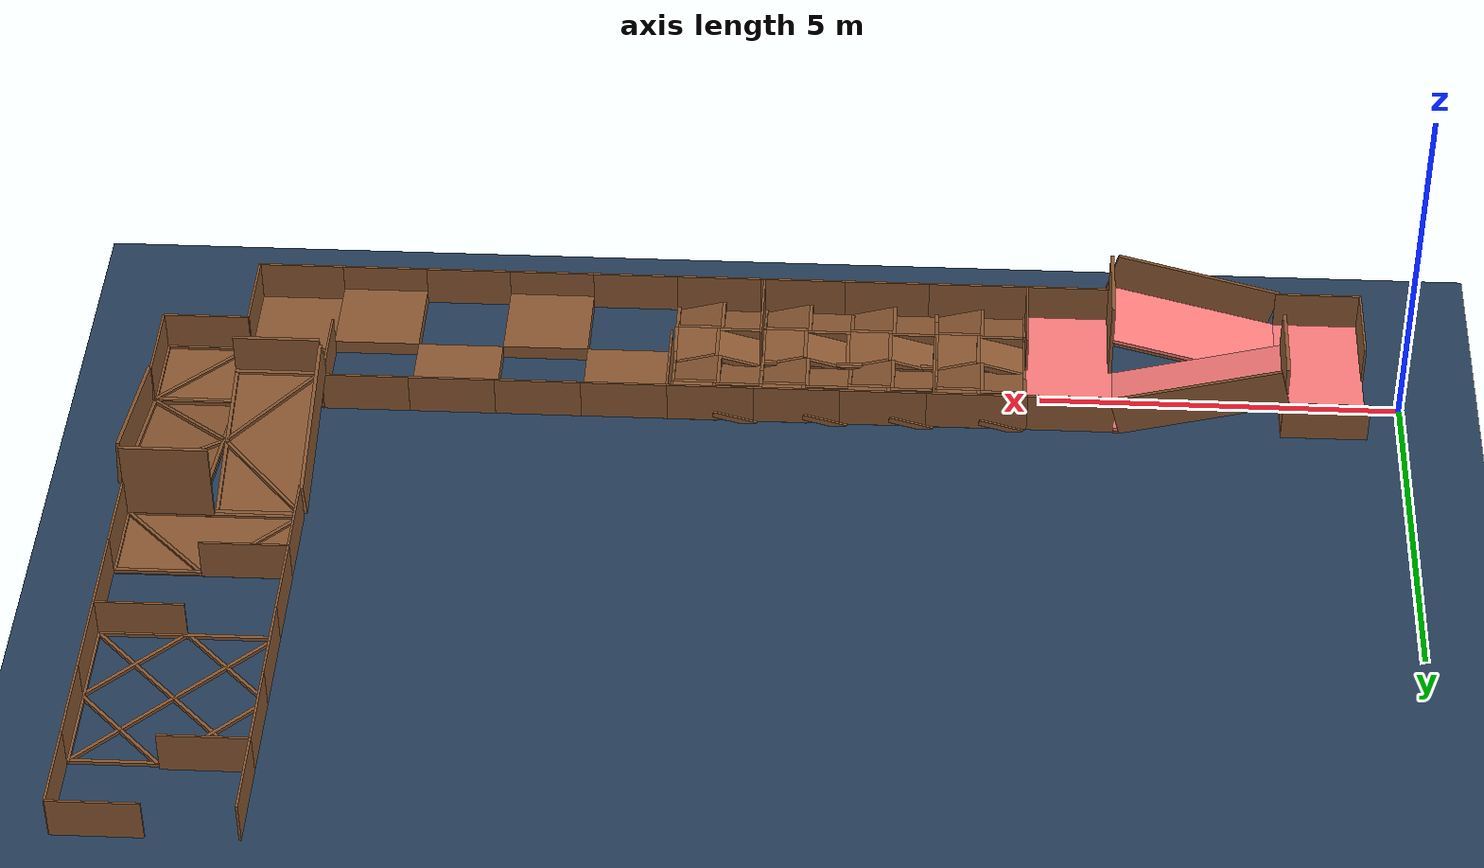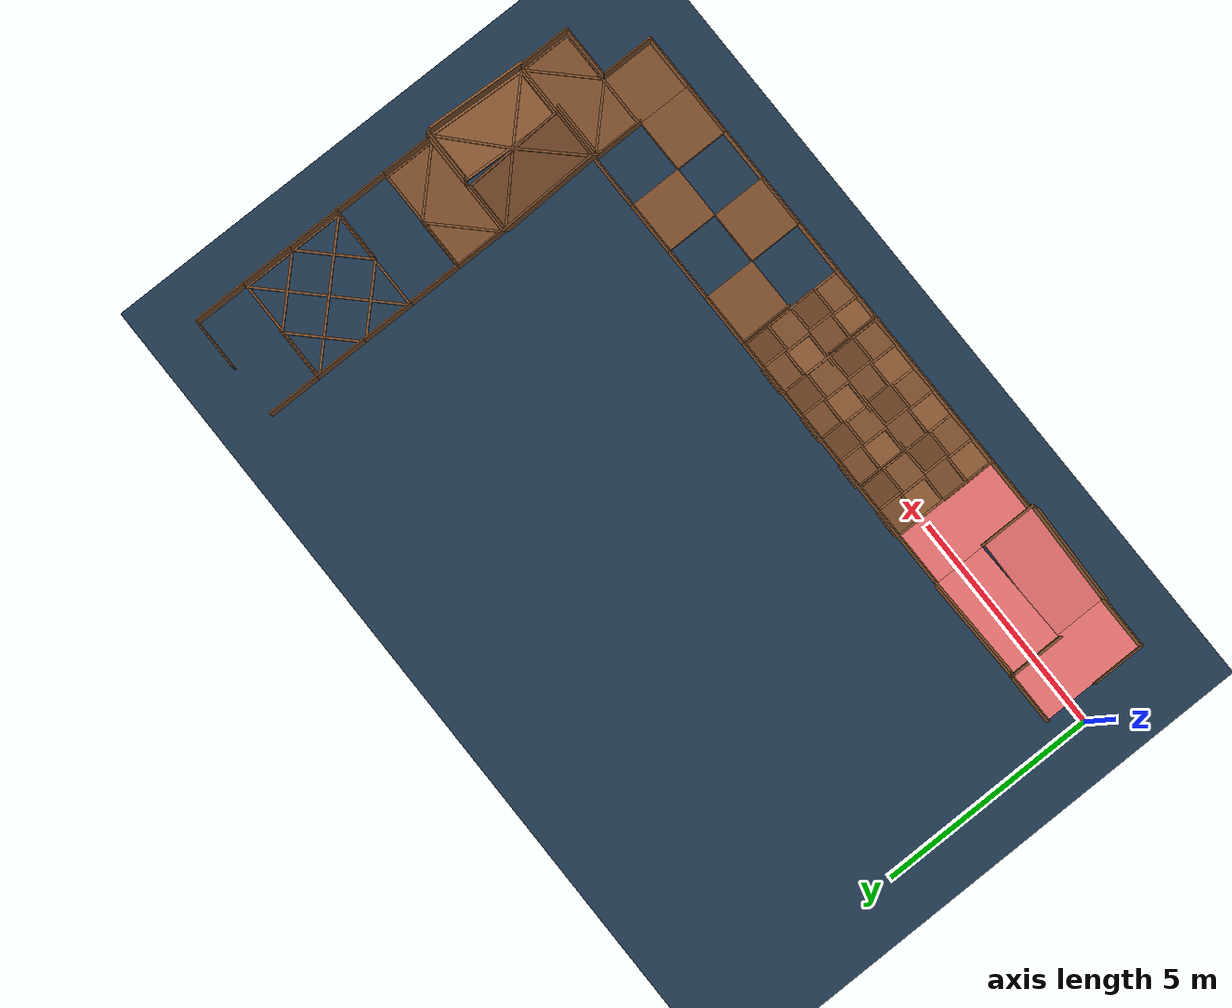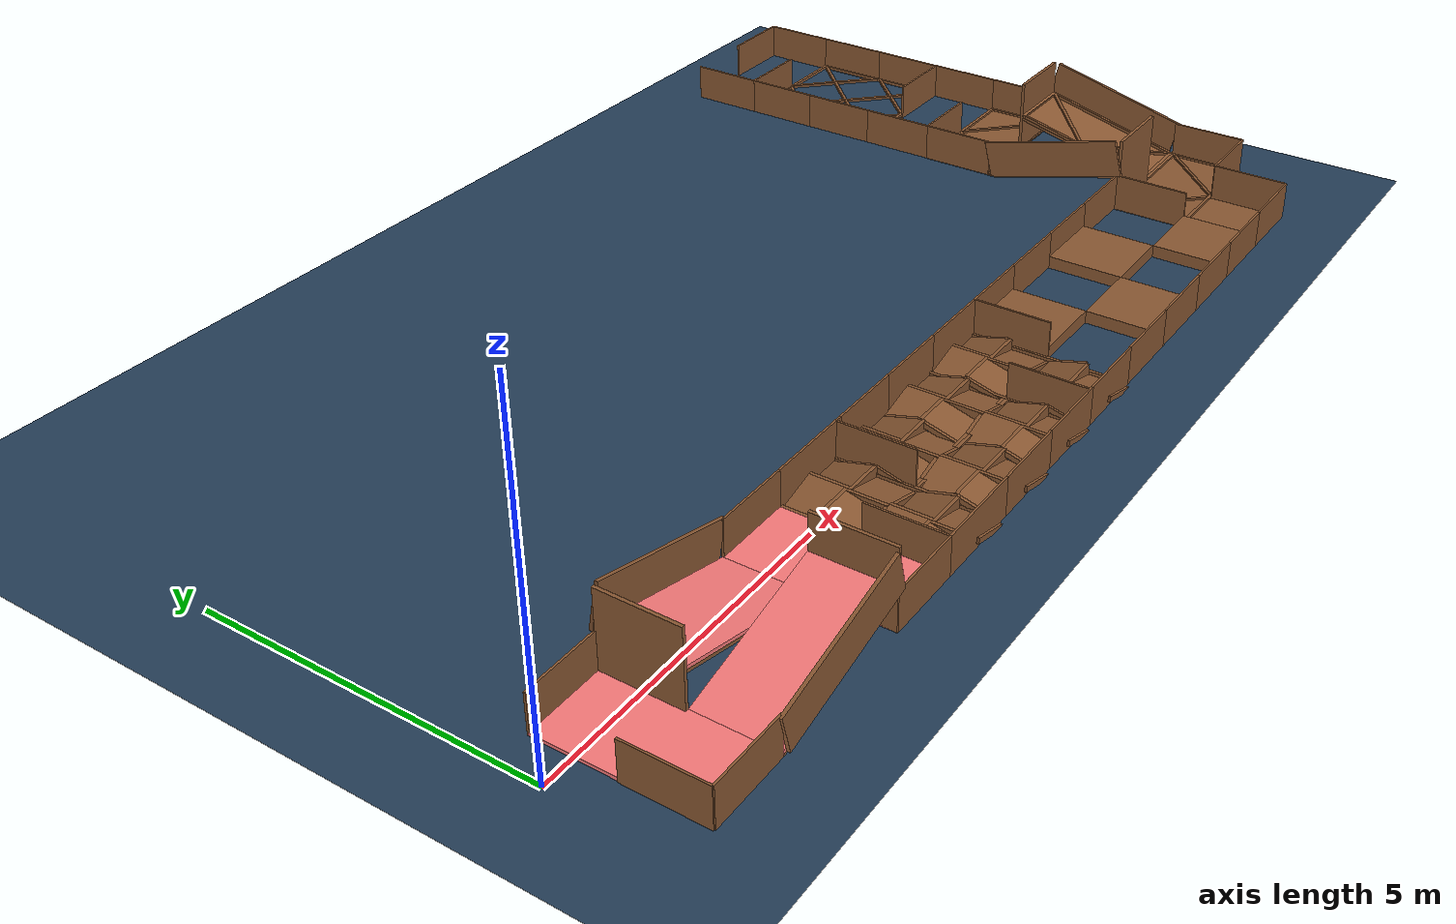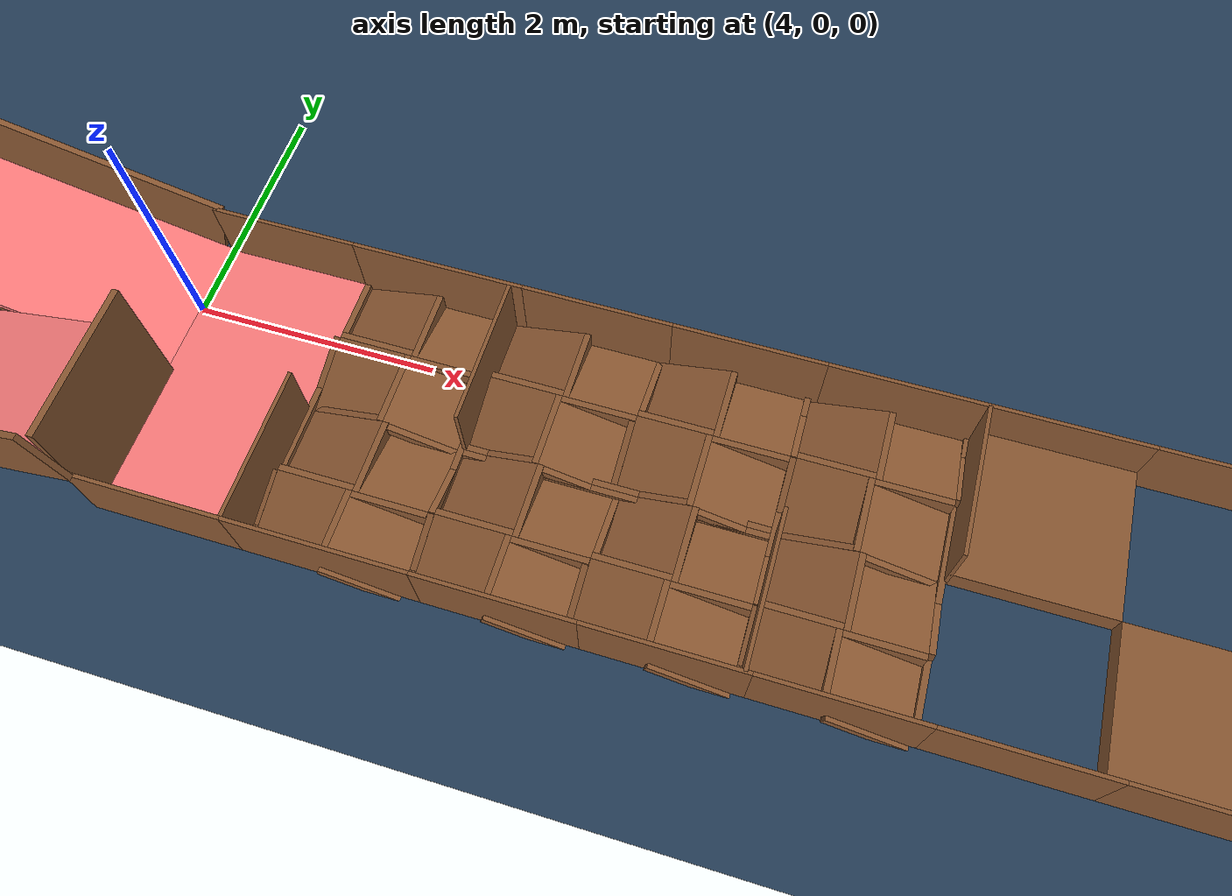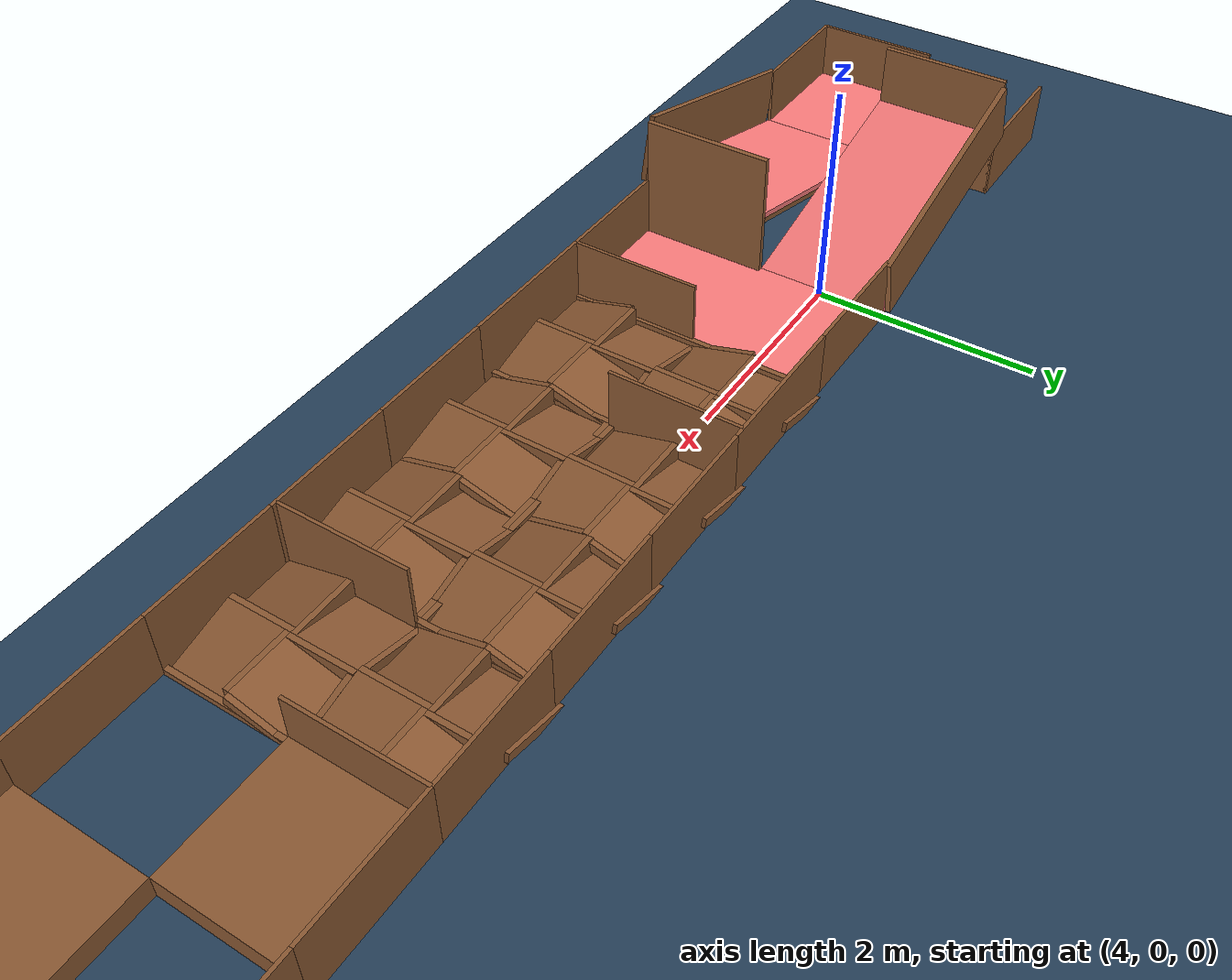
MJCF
<mujoco model="go2_rl_track">
  <statistic center="0 0 0.1" extent="0.8" />
  <visual>
    <headlight diffuse="0.6 0.6 0.6" ambient="0.3 0.3 0.3" specular="0 0 0" />
    <rgba haze="0.15 0.25 0.35 1" />
    <global azimuth="-130" elevation="-20" />
  </visual>
  <asset>
    <texture type="skybox" builtin="gradient" rgb1="0.3 0.5 0.7" rgb2="0 0 0" width="512" height="3072" />
    <texture type="2d" name="groundplane" builtin="checker" mark="edge" rgb1="0.2 0.3 0.4" rgb2="0.1 0.2 0.3" markrgb="0.8 0.8 0.8" width="300" height="300" />
    <material name="groundplane" texture="groundplane" texuniform="true" texrepeat="5 5" reflectance="0.0" />
    <texture name="wood_tex" type="2d" builtin="flat" rgb1="0.55 0.35 0.2" width="512" height="512" />
    <material name="wood_mat" texture="wood_tex" specular="0.2" shininess="0.1" rgba="1 1 1 1" />
    <texture name="sponge_tex" type="2d" builtin="flat" rgb1="1.0 0.7 0.7" width="512" height="512" />
    <material name="mat_sponge" texture="sponge_tex" specular="0.1" shininess="0.1" rgba="1 0.7 0.7 1" />
  </asset>
  <worldbody>
    <light pos="0 0 1.5" dir="0 0 -1" directional="true" />
    <geom name="go2_rl_track_0_collision" size="0 0 0.05" type="plane" group="3" contype="1" conaffinity="1" rgba="0.2 0.8 0.3 0.001" />
    <geom pos="2.833740429450787 2.220446049250313e-16 0.27579632720971" type="box" size="1.1981652640600127 0.6 0.025" quat="6.074277307224726e-17 0.12620041281310998 -7.727546580132487e-18 0.9920047660197004" friction="0.5 0.005 0.0001" name="go2_rl_track_1_collision" group="3" contype="1" conaffinity="1" rgba="0.2 0.8 0.3 0.001" />
    <geom pos="1.6550000000000002 2.220446049250313e-16 0.6" type="box" size="0.025 0.6 0.6" quat="6.123233995736766e-17 0.0 0.0 1.0" friction="0.5 0.005 0.0001" name="go2_rl_track_2_collision" group="3" contype="1" conaffinity="1" rgba="0.2 0.8 0.3 0.001" />
    <geom pos="2.833740429450787 0.6250000000000002 0.60079632720971" type="box" size="1.1981652640600127 0.025 0.3" quat="6.074277307224726e-17 0.12620041281310998 -7.727546580132487e-18 0.9920047660197004" friction="0.5 0.005 0.0001" name="go2_rl_track_3_collision" group="3" contype="1" conaffinity="1" rgba="0.2 0.8 0.3 0.001" />
    <geom pos="2.846259570549213 -1.2 0.27579632720971" type="box" size="1.1981652640600127 0.6 0.025" quat="0.9920047660197004 0.0 -0.12620041281310998 0.0" friction="0.5 0.005 0.0001" name="go2_rl_track_4_collision" group="3" contype="1" conaffinity="1" rgba="0.2 0.8 0.3 0.001" />
    <geom pos="4.025 -1.2 0.6" type="box" size="0.025 0.6 0.6" quat="1.0 0.0 0.0 0.0" friction="0.5 0.005 0.0001" name="go2_rl_track_5_collision" group="3" contype="1" conaffinity="1" rgba="0.2 0.8 0.3 0.001" />
    <geom pos="2.846259570549213 -1.825 0.60079632720971" type="box" size="1.1981652640600127 0.025 0.3" quat="0.9920047660197004 0.0 -0.12620041281310998 0.0" friction="0.5 0.005 0.0001" name="go2_rl_track_6_collision" group="3" contype="1" conaffinity="1" rgba="0.2 0.8 0.3 0.001" />
    <geom pos="4.6 -1.7999999999999998 0.3" type="box" size="0.6 0.3 0.015" quat="0.7071067811865476 0.7071067811865476 0.0 0.0" friction="0.5 0.005 0.0001" name="go2_rl_track_7_collision" group="3" contype="1" conaffinity="1" rgba="0.2 0.8 0.3 0.001" />
    <geom pos="1.08 -1.7999999999999998 0.3" type="box" size="0.6 0.3 0.015" quat="0.7071067811865476 0.7071067811865476 0.0 0.0" friction="0.5 0.005 0.0001" name="go2_rl_track_8_collision" group="3" contype="1" conaffinity="1" rgba="0.2 0.8 0.3 0.001" />
    <geom pos="4.6 0.6000000000000001 0.3" type="box" size="0.6 0.3 0.015" quat="0.7071067811865476 0.7071067811865476 0.0 0.0" friction="0.5 0.005 0.0001" name="go2_rl_track_9_collision" group="3" contype="1" conaffinity="1" rgba="0.2 0.8 0.3 0.001" />
    <geom pos="1.08 0.6000000000000001 0.3" type="box" size="0.6 0.3 0.015" quat="0.7071067811865476 0.7071067811865476 0.0 0.0" friction="0.5 0.005 0.0001" name="go2_rl_track_10_collision" group="3" contype="1" conaffinity="1" rgba="0.2 0.8 0.3 0.001" />
    <geom pos="0.48 -1.2 0.3" type="box" size="0.3 0.6 0.015" quat="0.7071067811865476 0.0 0.7071067811865476 0.0" friction="0.5 0.005 0.0001" name="go2_rl_track_11_collision" group="3" contype="1" conaffinity="1" rgba="0.2 0.8 0.3 0.001" />
    <geom pos="1.08 -0.6 0.025" type="box" size="0.6 1.2 0.025" quat="1.0 0.0 0.0 0.0" solref="0.03 1" priority="1" solmix="1" friction="1.2 0.005 0.0001" name="go2_rl_track_12_collision" group="3" contype="1" conaffinity="1" rgba="0.2 0.8 0.3 0.001" />
    <geom pos="4.6 -0.6 0.025" type="box" size="0.6 1.2 0.025" quat="1.0 0.0 0.0 0.0" solref="0.03 1" priority="1" solmix="1" friction="1.2 0.005 0.0001" name="go2_rl_track_13_collision" group="3" contype="1" conaffinity="1" rgba="0.2 0.8 0.3 0.001" />
    <geom pos="2.833740429450787 2.220446049250313e-16 0.32579632720970997" type="box" size="1.1981652640600127 0.6 0.025" quat="6.074277307224726e-17 0.12620041281310998 -7.727546580132487e-18 0.9920047660197004" solref="0.03 1" priority="1" solmix="1" friction="1.2 0.005 0.0001" name="go2_rl_track_14_collision" group="3" contype="1" conaffinity="1" rgba="0.2 0.8 0.3 0.001" />
    <geom pos="2.846259570549213 -1.2 0.32579632720970997" type="box" size="1.1981652640600127 0.6 0.025" quat="0.9920047660197004 0.0 -0.12620041281310998 0.0" solref="0.03 1" priority="1" solmix="1" friction="1.2 0.005 0.0001" name="go2_rl_track_15_collision" group="3" contype="1" conaffinity="1" rgba="0.2 0.8 0.3 0.001" />
    <geom pos="5.225 -0.6 0.0" type="box" size="1.2 0.025 0.05" quat="0.7071067811865476 0.0 0.0 0.7071067811865476" friction="0.5 0.005 0.0001" name="go2_rl_track_16_collision" group="3" contype="1" conaffinity="1" rgba="0.2 0.8 0.3 0.001" />
    <geom pos="5.55 -1.4934084623528479 0.05788461836407774" type="box" size="0.311004823113726 0.3 0.025" quat="0.7008236699478855 0.09405415270352165 -0.09405415270352165 0.7008236699478855" friction="0.5 0.005 0.0001" name="go2_rl_track_17_collision" group="3" contype="1" conaffinity="1" rgba="0.2 0.8 0.3 0.001" />
    <geom pos="5.55 -1.1749999999999998 0.082" type="box" size="0.025 0.3 0.082" quat="0.7071067811865476 0.0 0.0 0.7071067811865476" friction="0.5 0.005 0.0001" name="go2_rl_track_18_collision" group="3" contype="1" conaffinity="1" rgba="0.2 0.8 0.3 0.001" />
    <geom pos="5.875 -1.4934084623528479 0.04188461836407773" type="box" size="0.311004823113726 0.025 0.041" quat="0.7008236699478855 0.09405415270352165 -0.09405415270352165 0.7008236699478855" friction="0.5 0.005 0.0001" name="go2_rl_track_19_collision" group="3" contype="1" conaffinity="1" rgba="0.2 0.8 0.3 0.001" />
    <geom pos="5.225 -1.4934084623528479 0.04188461836407773" type="box" size="0.311004823113726 0.025 0.041" quat="0.7008236699478855 0.09405415270352165 -0.09405415270352165 0.7008236699478855" friction="0.5 0.005 0.0001" name="go2_rl_track_20_collision" group="3" contype="1" conaffinity="1" rgba="0.2 0.8 0.3 0.001" />
    <geom pos="5.556591537647153 -0.8999999999999999 0.05788461836407774" type="box" size="0.311004823113726 0.3 0.025" quat="0.9911143388723852 0.0 -0.1330126583508304 0.0" friction="0.5 0.005 0.0001" name="go2_rl_track_21_collision" group="3" contype="1" conaffinity="1" rgba="0.2 0.8 0.3 0.001" />
    <geom pos="5.875 -0.8999999999999999 0.082" type="box" size="0.025 0.3 0.082" quat="1.0 0.0 0.0 0.0" friction="0.5 0.005 0.0001" name="go2_rl_track_22_collision" group="3" contype="1" conaffinity="1" rgba="0.2 0.8 0.3 0.001" />
    <geom pos="5.556591537647153 -1.225 0.04188461836407773" type="box" size="0.311004823113726 0.025 0.041" quat="0.9911143388723852 0.0 -0.1330126583508304 0.0" friction="0.5 0.005 0.0001" name="go2_rl_track_23_collision" group="3" contype="1" conaffinity="1" rgba="0.2 0.8 0.3 0.001" />
    <geom pos="5.556591537647153 -0.575 0.04188461836407773" type="box" size="0.311004823113726 0.025 0.041" quat="0.9911143388723852 0.0 -0.1330126583508304 0.0" friction="0.5 0.005 0.0001" name="go2_rl_track_24_collision" group="3" contype="1" conaffinity="1" rgba="0.2 0.8 0.3 0.001" />
    <geom pos="6.143408462352848 -1.5 0.05788461836407774" type="box" size="0.311004823113726 0.3 0.025" quat="6.068825013445559e-17 0.1330126583508304 -8.144676314771245e-18 0.9911143388723852" friction="0.5 0.005 0.0001" name="go2_rl_track_25_collision" group="3" contype="1" conaffinity="1" rgba="0.2 0.8 0.3 0.001" />
    <geom pos="5.825 -1.5 0.082" type="box" size="0.025 0.3 0.082" quat="6.123233995736766e-17 0.0 0.0 1.0" friction="0.5 0.005 0.0001" name="go2_rl_track_26_collision" group="3" contype="1" conaffinity="1" rgba="0.2 0.8 0.3 0.001" />
    <geom pos="6.143408462352848 -1.1749999999999998 0.04188461836407773" type="box" size="0.311004823113726 0.025 0.041" quat="6.068825013445559e-17 0.1330126583508304 -8.144676314771245e-18 0.9911143388723852" friction="0.5 0.005 0.0001" name="go2_rl_track_27_collision" group="3" contype="1" conaffinity="1" rgba="0.2 0.8 0.3 0.001" />
    <geom pos="6.143408462352848 -1.825 0.04188461836407773" type="box" size="0.311004823113726 0.025 0.041" quat="6.068825013445559e-17 0.1330126583508304 -8.144676314771245e-18 0.9911143388723852" friction="0.5 0.005 0.0001" name="go2_rl_track_28_collision" group="3" contype="1" conaffinity="1" rgba="0.2 0.8 0.3 0.001" />
    <geom pos="6.15 -0.9065915376471521 0.05788461836407774" type="box" size="0.311004823113726 0.3 0.025" quat="-0.7008236699478854 0.09405415270352165 0.09405415270352163 0.7008236699478855" friction="0.5 0.005 0.0001" name="go2_rl_track_29_collision" group="3" contype="1" conaffinity="1" rgba="0.2 0.8 0.3 0.001" />
    <geom pos="6.15 -1.225 0.082" type="box" size="0.025 0.3 0.082" quat="-0.7071067811865475 -0.0 0.0 0.7071067811865476" friction="0.5 0.005 0.0001" name="go2_rl_track_30_collision" group="3" contype="1" conaffinity="1" rgba="0.2 0.8 0.3 0.001" />
    <geom pos="5.824999999999999 -0.9065915376471521 0.04188461836407773" type="box" size="0.311004823113726 0.025 0.041" quat="-0.7008236699478854 0.09405415270352165 0.09405415270352163 0.7008236699478855" friction="0.5 0.005 0.0001" name="go2_rl_track_31_collision" group="3" contype="1" conaffinity="1" rgba="0.2 0.8 0.3 0.001" />
    <geom pos="6.475 -0.9065915376471521 0.04188461836407773" type="box" size="0.311004823113726 0.025 0.041" quat="-0.7008236699478854 0.09405415270352165 0.09405415270352163 0.7008236699478855" friction="0.5 0.005 0.0001" name="go2_rl_track_32_collision" group="3" contype="1" conaffinity="1" rgba="0.2 0.8 0.3 0.001" />
    <geom pos="5.55 -0.2934084623528479 0.05788461836407774" type="box" size="0.311004823113726 0.3 0.025" quat="0.7008236699478855 0.09405415270352165 -0.09405415270352165 0.7008236699478855" friction="0.5 0.005 0.0001" name="go2_rl_track_33_collision" group="3" contype="1" conaffinity="1" rgba="0.2 0.8 0.3 0.001" />
    <geom pos="5.55 0.025000000000000133 0.082" type="box" size="0.025 0.3 0.082" quat="0.7071067811865476 0.0 0.0 0.7071067811865476" friction="0.5 0.005 0.0001" name="go2_rl_track_34_collision" group="3" contype="1" conaffinity="1" rgba="0.2 0.8 0.3 0.001" />
    <geom pos="5.875 -0.2934084623528479 0.04188461836407773" type="box" size="0.311004823113726 0.025 0.041" quat="0.7008236699478855 0.09405415270352165 -0.09405415270352165 0.7008236699478855" friction="0.5 0.005 0.0001" name="go2_rl_track_35_collision" group="3" contype="1" conaffinity="1" rgba="0.2 0.8 0.3 0.001" />
    <geom pos="5.225 -0.2934084623528479 0.04188461836407773" type="box" size="0.311004823113726 0.025 0.041" quat="0.7008236699478855 0.09405415270352165 -0.09405415270352165 0.7008236699478855" friction="0.5 0.005 0.0001" name="go2_rl_track_36_collision" group="3" contype="1" conaffinity="1" rgba="0.2 0.8 0.3 0.001" />
    <geom pos="5.556591537647153 0.30000000000000004 0.05788461836407774" type="box" size="0.311004823113726 0.3 0.025" quat="0.9911143388723852 0.0 -0.1330126583508304 0.0" friction="0.5 0.005 0.0001" name="go2_rl_track_37_collision" group="3" contype="1" conaffinity="1" rgba="0.2 0.8 0.3 0.001" />
    <geom pos="5.875 0.30000000000000004 0.082" type="box" size="0.025 0.3 0.082" quat="1.0 0.0 0.0 0.0" friction="0.5 0.005 0.0001" name="go2_rl_track_38_collision" group="3" contype="1" conaffinity="1" rgba="0.2 0.8 0.3 0.001" />
    <geom pos="5.556591537647153 -0.02499999999999991 0.04188461836407773" type="box" size="0.311004823113726 0.025 0.041" quat="0.9911143388723852 0.0 -0.1330126583508304 0.0" friction="0.5 0.005 0.0001" name="go2_rl_track_39_collision" group="3" contype="1" conaffinity="1" rgba="0.2 0.8 0.3 0.001" />
    <geom pos="5.556591537647153 0.625 0.04188461836407773" type="box" size="0.311004823113726 0.025 0.041" quat="0.9911143388723852 0.0 -0.1330126583508304 0.0" friction="0.5 0.005 0.0001" name="go2_rl_track_40_collision" group="3" contype="1" conaffinity="1" rgba="0.2 0.8 0.3 0.001" />
    <geom pos="6.143408462352848 -0.30000000000000004 0.05788461836407774" type="box" size="0.311004823113726 0.3 0.025" quat="6.068825013445559e-17 0.1330126583508304 -8.144676314771245e-18 0.9911143388723852" friction="0.5 0.005 0.0001" name="go2_rl_track_41_collision" group="3" contype="1" conaffinity="1" rgba="0.2 0.8 0.3 0.001" />
    <geom pos="5.825 -0.29999999999999993 0.082" type="box" size="0.025 0.3 0.082" quat="6.123233995736766e-17 0.0 0.0 1.0" friction="0.5 0.005 0.0001" name="go2_rl_track_42_collision" group="3" contype="1" conaffinity="1" rgba="0.2 0.8 0.3 0.001" />
    <geom pos="6.143408462352848 0.025000000000000133 0.04188461836407773" type="box" size="0.311004823113726 0.025 0.041" quat="6.068825013445559e-17 0.1330126583508304 -8.144676314771245e-18 0.9911143388723852" friction="0.5 0.005 0.0001" name="go2_rl_track_43_collision" group="3" contype="1" conaffinity="1" rgba="0.2 0.8 0.3 0.001" />
    <geom pos="6.143408462352848 -0.625 0.04188461836407773" type="box" size="0.311004823113726 0.025 0.041" quat="6.068825013445559e-17 0.1330126583508304 -8.144676314771245e-18 0.9911143388723852" friction="0.5 0.005 0.0001" name="go2_rl_track_44_collision" group="3" contype="1" conaffinity="1" rgba="0.2 0.8 0.3 0.001" />
    <geom pos="6.15 0.2934084623528477 0.05788461836407774" type="box" size="0.311004823113726 0.3 0.025" quat="-0.7008236699478854 0.09405415270352165 0.09405415270352163 0.7008236699478855" friction="0.5 0.005 0.0001" name="go2_rl_track_45_collision" group="3" contype="1" conaffinity="1" rgba="0.2 0.8 0.3 0.001" />
    <geom pos="6.15 -0.025000000000000133 0.082" type="box" size="0.025 0.3 0.082" quat="-0.7071067811865475 -0.0 0.0 0.7071067811865476" friction="0.5 0.005 0.0001" name="go2_rl_track_46_collision" group="3" contype="1" conaffinity="1" rgba="0.2 0.8 0.3 0.001" />
    <geom pos="5.824999999999999 0.2934084623528479 0.04188461836407773" type="box" size="0.311004823113726 0.025 0.041" quat="-0.7008236699478854 0.09405415270352165 0.09405415270352163 0.7008236699478855" friction="0.5 0.005 0.0001" name="go2_rl_track_47_collision" group="3" contype="1" conaffinity="1" rgba="0.2 0.8 0.3 0.001" />
    <geom pos="6.475 0.2934084623528477 0.04188461836407773" type="box" size="0.311004823113726 0.025 0.041" quat="-0.7008236699478854 0.09405415270352165 0.09405415270352163 0.7008236699478855" friction="0.5 0.005 0.0001" name="go2_rl_track_48_collision" group="3" contype="1" conaffinity="1" rgba="0.2 0.8 0.3 0.001" />
    <geom pos="6.475 -0.6 0.0" type="box" size="1.2 0.025 0.05" quat="0.7071067811865476 0.0 0.0 0.7071067811865476" friction="0.5 0.005 0.0001" name="go2_rl_track_49_collision" group="3" contype="1" conaffinity="1" rgba="0.2 0.8 0.3 0.001" />
    <geom pos="6.800000000000001 -1.4934084623528479 0.05788461836407774" type="box" size="0.311004823113726 0.3 0.025" quat="0.7008236699478855 0.09405415270352165 -0.09405415270352165 0.7008236699478855" friction="0.5 0.005 0.0001" name="go2_rl_track_50_collision" group="3" contype="1" conaffinity="1" rgba="0.2 0.8 0.3 0.001" />
    <geom pos="6.800000000000001 -1.1749999999999998 0.082" type="box" size="0.025 0.3 0.082" quat="0.7071067811865476 0.0 0.0 0.7071067811865476" friction="0.5 0.005 0.0001" name="go2_rl_track_51_collision" group="3" contype="1" conaffinity="1" rgba="0.2 0.8 0.3 0.001" />
    <geom pos="7.125 -1.4934084623528479 0.04188461836407773" type="box" size="0.311004823113726 0.025 0.041" quat="0.7008236699478855 0.09405415270352165 -0.09405415270352165 0.7008236699478855" friction="0.5 0.005 0.0001" name="go2_rl_track_52_collision" group="3" contype="1" conaffinity="1" rgba="0.2 0.8 0.3 0.001" />
    <geom pos="6.475 -1.4934084623528479 0.04188461836407773" type="box" size="0.311004823113726 0.025 0.041" quat="0.7008236699478855 0.09405415270352165 -0.09405415270352165 0.7008236699478855" friction="0.5 0.005 0.0001" name="go2_rl_track_53_collision" group="3" contype="1" conaffinity="1" rgba="0.2 0.8 0.3 0.001" />
    <geom pos="6.806591537647153 -0.8999999999999999 0.05788461836407774" type="box" size="0.311004823113726 0.3 0.025" quat="0.9911143388723852 0.0 -0.1330126583508304 0.0" friction="0.5 0.005 0.0001" name="go2_rl_track_54_collision" group="3" contype="1" conaffinity="1" rgba="0.2 0.8 0.3 0.001" />
    <geom pos="7.125 -0.8999999999999999 0.082" type="box" size="0.025 0.3 0.082" quat="1.0 0.0 0.0 0.0" friction="0.5 0.005 0.0001" name="go2_rl_track_55_collision" group="3" contype="1" conaffinity="1" rgba="0.2 0.8 0.3 0.001" />
    <geom pos="6.806591537647153 -1.225 0.04188461836407773" type="box" size="0.311004823113726 0.025 0.041" quat="0.9911143388723852 0.0 -0.1330126583508304 0.0" friction="0.5 0.005 0.0001" name="go2_rl_track_56_collision" group="3" contype="1" conaffinity="1" rgba="0.2 0.8 0.3 0.001" />
    <geom pos="6.806591537647153 -0.575 0.04188461836407773" type="box" size="0.311004823113726 0.025 0.041" quat="0.9911143388723852 0.0 -0.1330126583508304 0.0" friction="0.5 0.005 0.0001" name="go2_rl_track_57_collision" group="3" contype="1" conaffinity="1" rgba="0.2 0.8 0.3 0.001" />
    <geom pos="7.393408462352848 -1.5 0.05788461836407774" type="box" size="0.311004823113726 0.3 0.025" quat="6.068825013445559e-17 0.1330126583508304 -8.144676314771245e-18 0.9911143388723852" friction="0.5 0.005 0.0001" name="go2_rl_track_58_collision" group="3" contype="1" conaffinity="1" rgba="0.2 0.8 0.3 0.001" />
    <geom pos="7.075 -1.5 0.082" type="box" size="0.025 0.3 0.082" quat="6.123233995736766e-17 0.0 0.0 1.0" friction="0.5 0.005 0.0001" name="go2_rl_track_59_collision" group="3" contype="1" conaffinity="1" rgba="0.2 0.8 0.3 0.001" />
    <geom pos="7.393408462352848 -1.1749999999999998 0.04188461836407773" type="box" size="0.311004823113726 0.025 0.041" quat="6.068825013445559e-17 0.1330126583508304 -8.144676314771245e-18 0.9911143388723852" friction="0.5 0.005 0.0001" name="go2_rl_track_60_collision" group="3" contype="1" conaffinity="1" rgba="0.2 0.8 0.3 0.001" />
    <geom pos="7.393408462352848 -1.825 0.04188461836407773" type="box" size="0.311004823113726 0.025 0.041" quat="6.068825013445559e-17 0.1330126583508304 -8.144676314771245e-18 0.9911143388723852" friction="0.5 0.005 0.0001" name="go2_rl_track_61_collision" group="3" contype="1" conaffinity="1" rgba="0.2 0.8 0.3 0.001" />
    <geom pos="7.4 -0.9065915376471521 0.05788461836407774" type="box" size="0.311004823113726 0.3 0.025" quat="-0.7008236699478854 0.09405415270352165 0.09405415270352163 0.7008236699478855" friction="0.5 0.005 0.0001" name="go2_rl_track_62_collision" group="3" contype="1" conaffinity="1" rgba="0.2 0.8 0.3 0.001" />
    <geom pos="7.4 -1.225 0.082" type="box" size="0.025 0.3 0.082" quat="-0.7071067811865475 -0.0 0.0 0.7071067811865476" friction="0.5 0.005 0.0001" name="go2_rl_track_63_collision" group="3" contype="1" conaffinity="1" rgba="0.2 0.8 0.3 0.001" />
    <geom pos="7.074999999999999 -0.9065915376471521 0.04188461836407773" type="box" size="0.311004823113726 0.025 0.041" quat="-0.7008236699478854 0.09405415270352165 0.09405415270352163 0.7008236699478855" friction="0.5 0.005 0.0001" name="go2_rl_track_64_collision" group="3" contype="1" conaffinity="1" rgba="0.2 0.8 0.3 0.001" />
    <geom pos="7.725 -0.9065915376471521 0.04188461836407773" type="box" size="0.311004823113726 0.025 0.041" quat="-0.7008236699478854 0.09405415270352165 0.09405415270352163 0.7008236699478855" friction="0.5 0.005 0.0001" name="go2_rl_track_65_collision" group="3" contype="1" conaffinity="1" rgba="0.2 0.8 0.3 0.001" />
    <geom pos="6.800000000000001 -0.2934084623528479 0.05788461836407774" type="box" size="0.311004823113726 0.3 0.025" quat="0.7008236699478855 0.09405415270352165 -0.09405415270352165 0.7008236699478855" friction="0.5 0.005 0.0001" name="go2_rl_track_66_collision" group="3" contype="1" conaffinity="1" rgba="0.2 0.8 0.3 0.001" />
    <geom pos="6.800000000000001 0.025000000000000133 0.082" type="box" size="0.025 0.3 0.082" quat="0.7071067811865476 0.0 0.0 0.7071067811865476" friction="0.5 0.005 0.0001" name="go2_rl_track_67_collision" group="3" contype="1" conaffinity="1" rgba="0.2 0.8 0.3 0.001" />
    <geom pos="7.125 -0.2934084623528479 0.04188461836407773" type="box" size="0.311004823113726 0.025 0.041" quat="0.7008236699478855 0.09405415270352165 -0.09405415270352165 0.7008236699478855" friction="0.5 0.005 0.0001" name="go2_rl_track_68_collision" group="3" contype="1" conaffinity="1" rgba="0.2 0.8 0.3 0.001" />
    <geom pos="6.475 -0.2934084623528479 0.04188461836407773" type="box" size="0.311004823113726 0.025 0.041" quat="0.7008236699478855 0.09405415270352165 -0.09405415270352165 0.7008236699478855" friction="0.5 0.005 0.0001" name="go2_rl_track_69_collision" group="3" contype="1" conaffinity="1" rgba="0.2 0.8 0.3 0.001" />
    <geom pos="6.806591537647153 0.30000000000000004 0.05788461836407774" type="box" size="0.311004823113726 0.3 0.025" quat="0.9911143388723852 0.0 -0.1330126583508304 0.0" friction="0.5 0.005 0.0001" name="go2_rl_track_70_collision" group="3" contype="1" conaffinity="1" rgba="0.2 0.8 0.3 0.001" />
    <geom pos="7.125 0.30000000000000004 0.082" type="box" size="0.025 0.3 0.082" quat="1.0 0.0 0.0 0.0" friction="0.5 0.005 0.0001" name="go2_rl_track_71_collision" group="3" contype="1" conaffinity="1" rgba="0.2 0.8 0.3 0.001" />
    <geom pos="6.806591537647153 -0.02499999999999991 0.04188461836407773" type="box" size="0.311004823113726 0.025 0.041" quat="0.9911143388723852 0.0 -0.1330126583508304 0.0" friction="0.5 0.005 0.0001" name="go2_rl_track_72_collision" group="3" contype="1" conaffinity="1" rgba="0.2 0.8 0.3 0.001" />
    <geom pos="6.806591537647153 0.625 0.04188461836407773" type="box" size="0.311004823113726 0.025 0.041" quat="0.9911143388723852 0.0 -0.1330126583508304 0.0" friction="0.5 0.005 0.0001" name="go2_rl_track_73_collision" group="3" contype="1" conaffinity="1" rgba="0.2 0.8 0.3 0.001" />
    <geom pos="7.393408462352848 -0.30000000000000004 0.05788461836407774" type="box" size="0.311004823113726 0.3 0.025" quat="6.068825013445559e-17 0.1330126583508304 -8.144676314771245e-18 0.9911143388723852" friction="0.5 0.005 0.0001" name="go2_rl_track_74_collision" group="3" contype="1" conaffinity="1" rgba="0.2 0.8 0.3 0.001" />
    <geom pos="7.075 -0.29999999999999993 0.082" type="box" size="0.025 0.3 0.082" quat="6.123233995736766e-17 0.0 0.0 1.0" friction="0.5 0.005 0.0001" name="go2_rl_track_75_collision" group="3" contype="1" conaffinity="1" rgba="0.2 0.8 0.3 0.001" />
    <geom pos="7.393408462352848 0.025000000000000133 0.04188461836407773" type="box" size="0.311004823113726 0.025 0.041" quat="6.068825013445559e-17 0.1330126583508304 -8.144676314771245e-18 0.9911143388723852" friction="0.5 0.005 0.0001" name="go2_rl_track_76_collision" group="3" contype="1" conaffinity="1" rgba="0.2 0.8 0.3 0.001" />
    <geom pos="7.393408462352848 -0.625 0.04188461836407773" type="box" size="0.311004823113726 0.025 0.041" quat="6.068825013445559e-17 0.1330126583508304 -8.144676314771245e-18 0.9911143388723852" friction="0.5 0.005 0.0001" name="go2_rl_track_77_collision" group="3" contype="1" conaffinity="1" rgba="0.2 0.8 0.3 0.001" />
    <geom pos="7.4 0.2934084623528477 0.05788461836407774" type="box" size="0.311004823113726 0.3 0.025" quat="-0.7008236699478854 0.09405415270352165 0.09405415270352163 0.7008236699478855" friction="0.5 0.005 0.0001" name="go2_rl_track_78_collision" group="3" contype="1" conaffinity="1" rgba="0.2 0.8 0.3 0.001" />
    <geom pos="7.4 -0.025000000000000133 0.082" type="box" size="0.025 0.3 0.082" quat="-0.7071067811865475 -0.0 0.0 0.7071067811865476" friction="0.5 0.005 0.0001" name="go2_rl_track_79_collision" group="3" contype="1" conaffinity="1" rgba="0.2 0.8 0.3 0.001" />
    <geom pos="7.074999999999999 0.2934084623528479 0.04188461836407773" type="box" size="0.311004823113726 0.025 0.041" quat="-0.7008236699478854 0.09405415270352165 0.09405415270352163 0.7008236699478855" friction="0.5 0.005 0.0001" name="go2_rl_track_80_collision" group="3" contype="1" conaffinity="1" rgba="0.2 0.8 0.3 0.001" />
    <geom pos="7.725 0.2934084623528477 0.04188461836407773" type="box" size="0.311004823113726 0.025 0.041" quat="-0.7008236699478854 0.09405415270352165 0.09405415270352163 0.7008236699478855" friction="0.5 0.005 0.0001" name="go2_rl_track_81_collision" group="3" contype="1" conaffinity="1" rgba="0.2 0.8 0.3 0.001" />
    <geom pos="8.0 -1.4934084623528479 0.05788461836407774" type="box" size="0.311004823113726 0.3 0.025" quat="0.7008236699478855 0.09405415270352165 -0.09405415270352165 0.7008236699478855" friction="0.5 0.005 0.0001" name="go2_rl_track_82_collision" group="3" contype="1" conaffinity="1" rgba="0.2 0.8 0.3 0.001" />
    <geom pos="8.0 -1.1749999999999998 0.082" type="box" size="0.025 0.3 0.082" quat="0.7071067811865476 0.0 0.0 0.7071067811865476" friction="0.5 0.005 0.0001" name="go2_rl_track_83_collision" group="3" contype="1" conaffinity="1" rgba="0.2 0.8 0.3 0.001" />
    <geom pos="8.325 -1.4934084623528479 0.04188461836407773" type="box" size="0.311004823113726 0.025 0.041" quat="0.7008236699478855 0.09405415270352165 -0.09405415270352165 0.7008236699478855" friction="0.5 0.005 0.0001" name="go2_rl_track_84_collision" group="3" contype="1" conaffinity="1" rgba="0.2 0.8 0.3 0.001" />
    <geom pos="7.675 -1.4934084623528479 0.04188461836407773" type="box" size="0.311004823113726 0.025 0.041" quat="0.7008236699478855 0.09405415270352165 -0.09405415270352165 0.7008236699478855" friction="0.5 0.005 0.0001" name="go2_rl_track_85_collision" group="3" contype="1" conaffinity="1" rgba="0.2 0.8 0.3 0.001" />
    <geom pos="8.006591537647152 -0.8999999999999999 0.05788461836407774" type="box" size="0.311004823113726 0.3 0.025" quat="0.9911143388723852 0.0 -0.1330126583508304 0.0" friction="0.5 0.005 0.0001" name="go2_rl_track_86_collision" group="3" contype="1" conaffinity="1" rgba="0.2 0.8 0.3 0.001" />
    <geom pos="8.325 -0.8999999999999999 0.082" type="box" size="0.025 0.3 0.082" quat="1.0 0.0 0.0 0.0" friction="0.5 0.005 0.0001" name="go2_rl_track_87_collision" group="3" contype="1" conaffinity="1" rgba="0.2 0.8 0.3 0.001" />
    <geom pos="8.006591537647152 -1.225 0.04188461836407773" type="box" size="0.311004823113726 0.025 0.041" quat="0.9911143388723852 0.0 -0.1330126583508304 0.0" friction="0.5 0.005 0.0001" name="go2_rl_track_88_collision" group="3" contype="1" conaffinity="1" rgba="0.2 0.8 0.3 0.001" />
    <geom pos="8.006591537647152 -0.575 0.04188461836407773" type="box" size="0.311004823113726 0.025 0.041" quat="0.9911143388723852 0.0 -0.1330126583508304 0.0" friction="0.5 0.005 0.0001" name="go2_rl_track_89_collision" group="3" contype="1" conaffinity="1" rgba="0.2 0.8 0.3 0.001" />
    <geom pos="8.593408462352848 -1.5 0.05788461836407774" type="box" size="0.311004823113726 0.3 0.025" quat="6.068825013445559e-17 0.1330126583508304 -8.144676314771245e-18 0.9911143388723852" friction="0.5 0.005 0.0001" name="go2_rl_track_90_collision" group="3" contype="1" conaffinity="1" rgba="0.2 0.8 0.3 0.001" />
    <geom pos="8.274999999999999 -1.5 0.082" type="box" size="0.025 0.3 0.082" quat="6.123233995736766e-17 0.0 0.0 1.0" friction="0.5 0.005 0.0001" name="go2_rl_track_91_collision" group="3" contype="1" conaffinity="1" rgba="0.2 0.8 0.3 0.001" />
    <geom pos="8.593408462352848 -1.1749999999999998 0.04188461836407773" type="box" size="0.311004823113726 0.025 0.041" quat="6.068825013445559e-17 0.1330126583508304 -8.144676314771245e-18 0.9911143388723852" friction="0.5 0.005 0.0001" name="go2_rl_track_92_collision" group="3" contype="1" conaffinity="1" rgba="0.2 0.8 0.3 0.001" />
    <geom pos="8.593408462352848 -1.825 0.04188461836407773" type="box" size="0.311004823113726 0.025 0.041" quat="6.068825013445559e-17 0.1330126583508304 -8.144676314771245e-18 0.9911143388723852" friction="0.5 0.005 0.0001" name="go2_rl_track_93_collision" group="3" contype="1" conaffinity="1" rgba="0.2 0.8 0.3 0.001" />
    <geom pos="8.6 -0.9065915376471521 0.05788461836407774" type="box" size="0.311004823113726 0.3 0.025" quat="-0.7008236699478854 0.09405415270352165 0.09405415270352163 0.7008236699478855" friction="0.5 0.005 0.0001" name="go2_rl_track_94_collision" group="3" contype="1" conaffinity="1" rgba="0.2 0.8 0.3 0.001" />
    <geom pos="8.6 -1.225 0.082" type="box" size="0.025 0.3 0.082" quat="-0.7071067811865475 -0.0 0.0 0.7071067811865476" friction="0.5 0.005 0.0001" name="go2_rl_track_95_collision" group="3" contype="1" conaffinity="1" rgba="0.2 0.8 0.3 0.001" />
    <geom pos="8.274999999999999 -0.9065915376471521 0.04188461836407773" type="box" size="0.311004823113726 0.025 0.041" quat="-0.7008236699478854 0.09405415270352165 0.09405415270352163 0.7008236699478855" friction="0.5 0.005 0.0001" name="go2_rl_track_96_collision" group="3" contype="1" conaffinity="1" rgba="0.2 0.8 0.3 0.001" />
    <geom pos="8.925 -0.9065915376471521 0.04188461836407773" type="box" size="0.311004823113726 0.025 0.041" quat="-0.7008236699478854 0.09405415270352165 0.09405415270352163 0.7008236699478855" friction="0.5 0.005 0.0001" name="go2_rl_track_97_collision" group="3" contype="1" conaffinity="1" rgba="0.2 0.8 0.3 0.001" />
    <geom pos="8.0 -0.2934084623528479 0.05788461836407774" type="box" size="0.311004823113726 0.3 0.025" quat="0.7008236699478855 0.09405415270352165 -0.09405415270352165 0.7008236699478855" friction="0.5 0.005 0.0001" name="go2_rl_track_98_collision" group="3" contype="1" conaffinity="1" rgba="0.2 0.8 0.3 0.001" />
    <geom pos="8.0 0.025000000000000133 0.082" type="box" size="0.025 0.3 0.082" quat="0.7071067811865476 0.0 0.0 0.7071067811865476" friction="0.5 0.005 0.0001" name="go2_rl_track_99_collision" group="3" contype="1" conaffinity="1" rgba="0.2 0.8 0.3 0.001" />
    <geom pos="8.325 -0.2934084623528479 0.04188461836407773" type="box" size="0.311004823113726 0.025 0.041" quat="0.7008236699478855 0.09405415270352165 -0.09405415270352165 0.7008236699478855" friction="0.5 0.005 0.0001" name="go2_rl_track_100_collision" group="3" contype="1" conaffinity="1" rgba="0.2 0.8 0.3 0.001" />
    <geom pos="7.675 -0.2934084623528479 0.04188461836407773" type="box" size="0.311004823113726 0.025 0.041" quat="0.7008236699478855 0.09405415270352165 -0.09405415270352165 0.7008236699478855" friction="0.5 0.005 0.0001" name="go2_rl_track_101_collision" group="3" contype="1" conaffinity="1" rgba="0.2 0.8 0.3 0.001" />
    <geom pos="8.006591537647152 0.30000000000000004 0.05788461836407774" type="box" size="0.311004823113726 0.3 0.025" quat="0.9911143388723852 0.0 -0.1330126583508304 0.0" friction="0.5 0.005 0.0001" name="go2_rl_track_102_collision" group="3" contype="1" conaffinity="1" rgba="0.2 0.8 0.3 0.001" />
    <geom pos="8.325 0.30000000000000004 0.082" type="box" size="0.025 0.3 0.082" quat="1.0 0.0 0.0 0.0" friction="0.5 0.005 0.0001" name="go2_rl_track_103_collision" group="3" contype="1" conaffinity="1" rgba="0.2 0.8 0.3 0.001" />
    <geom pos="8.006591537647152 -0.02499999999999991 0.04188461836407773" type="box" size="0.311004823113726 0.025 0.041" quat="0.9911143388723852 0.0 -0.1330126583508304 0.0" friction="0.5 0.005 0.0001" name="go2_rl_track_104_collision" group="3" contype="1" conaffinity="1" rgba="0.2 0.8 0.3 0.001" />
    <geom pos="8.006591537647152 0.625 0.04188461836407773" type="box" size="0.311004823113726 0.025 0.041" quat="0.9911143388723852 0.0 -0.1330126583508304 0.0" friction="0.5 0.005 0.0001" name="go2_rl_track_105_collision" group="3" contype="1" conaffinity="1" rgba="0.2 0.8 0.3 0.001" />
    <geom pos="8.593408462352848 -0.30000000000000004 0.05788461836407774" type="box" size="0.311004823113726 0.3 0.025" quat="6.068825013445559e-17 0.1330126583508304 -8.144676314771245e-18 0.9911143388723852" friction="0.5 0.005 0.0001" name="go2_rl_track_106_collision" group="3" contype="1" conaffinity="1" rgba="0.2 0.8 0.3 0.001" />
    <geom pos="8.274999999999999 -0.29999999999999993 0.082" type="box" size="0.025 0.3 0.082" quat="6.123233995736766e-17 0.0 0.0 1.0" friction="0.5 0.005 0.0001" name="go2_rl_track_107_collision" group="3" contype="1" conaffinity="1" rgba="0.2 0.8 0.3 0.001" />
    <geom pos="8.593408462352848 0.025000000000000133 0.04188461836407773" type="box" size="0.311004823113726 0.025 0.041" quat="6.068825013445559e-17 0.1330126583508304 -8.144676314771245e-18 0.9911143388723852" friction="0.5 0.005 0.0001" name="go2_rl_track_108_collision" group="3" contype="1" conaffinity="1" rgba="0.2 0.8 0.3 0.001" />
    <geom pos="8.593408462352848 -0.625 0.04188461836407773" type="box" size="0.311004823113726 0.025 0.041" quat="6.068825013445559e-17 0.1330126583508304 -8.144676314771245e-18 0.9911143388723852" friction="0.5 0.005 0.0001" name="go2_rl_track_109_collision" group="3" contype="1" conaffinity="1" rgba="0.2 0.8 0.3 0.001" />
    <geom pos="8.6 0.2934084623528477 0.05788461836407774" type="box" size="0.311004823113726 0.3 0.025" quat="-0.7008236699478854 0.09405415270352165 0.09405415270352163 0.7008236699478855" friction="0.5 0.005 0.0001" name="go2_rl_track_110_collision" group="3" contype="1" conaffinity="1" rgba="0.2 0.8 0.3 0.001" />
    <geom pos="8.6 -0.025000000000000133 0.082" type="box" size="0.025 0.3 0.082" quat="-0.7071067811865475 -0.0 0.0 0.7071067811865476" friction="0.5 0.005 0.0001" name="go2_rl_track_111_collision" group="3" contype="1" conaffinity="1" rgba="0.2 0.8 0.3 0.001" />
    <geom pos="8.274999999999999 0.2934084623528479 0.04188461836407773" type="box" size="0.311004823113726 0.025 0.041" quat="-0.7008236699478854 0.09405415270352165 0.09405415270352163 0.7008236699478855" friction="0.5 0.005 0.0001" name="go2_rl_track_112_collision" group="3" contype="1" conaffinity="1" rgba="0.2 0.8 0.3 0.001" />
    <geom pos="8.925 0.2934084623528477 0.04188461836407773" type="box" size="0.311004823113726 0.025 0.041" quat="-0.7008236699478854 0.09405415270352165 0.09405415270352163 0.7008236699478855" friction="0.5 0.005 0.0001" name="go2_rl_track_113_collision" group="3" contype="1" conaffinity="1" rgba="0.2 0.8 0.3 0.001" />
    <geom pos="7.7 -0.625 0.0" type="box" size="1.2 0.025 0.05" quat="1.0 0.0 0.0 0.0" friction="0.5 0.005 0.0001" name="go2_rl_track_114_collision" group="3" contype="1" conaffinity="1" rgba="0.2 0.8 0.3 0.001" />
    <geom pos="7.7 -0.575 0.0" type="box" size="1.2 0.025 0.05" quat="1.0 0.0 0.0 0.0" friction="0.5 0.005 0.0001" name="go2_rl_track_115_collision" group="3" contype="1" conaffinity="1" rgba="0.2 0.8 0.3 0.001" />
    <geom pos="8.925 -0.6 0.0" type="box" size="1.2 0.025 0.05" quat="0.7071067811865476 0.0 0.0 0.7071067811865476" friction="0.5 0.005 0.0001" name="go2_rl_track_116_collision" group="3" contype="1" conaffinity="1" rgba="0.2 0.8 0.3 0.001" />
    <geom pos="9.25 -1.4934084623528479 0.05788461836407774" type="box" size="0.311004823113726 0.3 0.025" quat="0.7008236699478855 0.09405415270352165 -0.09405415270352165 0.7008236699478855" friction="0.5 0.005 0.0001" name="go2_rl_track_117_collision" group="3" contype="1" conaffinity="1" rgba="0.2 0.8 0.3 0.001" />
    <geom pos="9.25 -1.1749999999999998 0.082" type="box" size="0.025 0.3 0.082" quat="0.7071067811865476 0.0 0.0 0.7071067811865476" friction="0.5 0.005 0.0001" name="go2_rl_track_118_collision" group="3" contype="1" conaffinity="1" rgba="0.2 0.8 0.3 0.001" />
    <geom pos="9.575 -1.4934084623528479 0.04188461836407773" type="box" size="0.311004823113726 0.025 0.041" quat="0.7008236699478855 0.09405415270352165 -0.09405415270352165 0.7008236699478855" friction="0.5 0.005 0.0001" name="go2_rl_track_119_collision" group="3" contype="1" conaffinity="1" rgba="0.2 0.8 0.3 0.001" />
    <geom pos="8.925 -1.4934084623528479 0.04188461836407773" type="box" size="0.311004823113726 0.025 0.041" quat="0.7008236699478855 0.09405415270352165 -0.09405415270352165 0.7008236699478855" friction="0.5 0.005 0.0001" name="go2_rl_track_120_collision" group="3" contype="1" conaffinity="1" rgba="0.2 0.8 0.3 0.001" />
    <geom pos="9.256591537647152 -0.8999999999999999 0.05788461836407774" type="box" size="0.311004823113726 0.3 0.025" quat="0.9911143388723852 0.0 -0.1330126583508304 0.0" friction="0.5 0.005 0.0001" name="go2_rl_track_121_collision" group="3" contype="1" conaffinity="1" rgba="0.2 0.8 0.3 0.001" />
    <geom pos="9.575 -0.8999999999999999 0.082" type="box" size="0.025 0.3 0.082" quat="1.0 0.0 0.0 0.0" friction="0.5 0.005 0.0001" name="go2_rl_track_122_collision" group="3" contype="1" conaffinity="1" rgba="0.2 0.8 0.3 0.001" />
    <geom pos="9.256591537647152 -1.225 0.04188461836407773" type="box" size="0.311004823113726 0.025 0.041" quat="0.9911143388723852 0.0 -0.1330126583508304 0.0" friction="0.5 0.005 0.0001" name="go2_rl_track_123_collision" group="3" contype="1" conaffinity="1" rgba="0.2 0.8 0.3 0.001" />
    <geom pos="9.256591537647152 -0.575 0.04188461836407773" type="box" size="0.311004823113726 0.025 0.041" quat="0.9911143388723852 0.0 -0.1330126583508304 0.0" friction="0.5 0.005 0.0001" name="go2_rl_track_124_collision" group="3" contype="1" conaffinity="1" rgba="0.2 0.8 0.3 0.001" />
    <geom pos="9.843408462352848 -1.5 0.05788461836407774" type="box" size="0.311004823113726 0.3 0.025" quat="6.068825013445559e-17 0.1330126583508304 -8.144676314771245e-18 0.9911143388723852" friction="0.5 0.005 0.0001" name="go2_rl_track_125_collision" group="3" contype="1" conaffinity="1" rgba="0.2 0.8 0.3 0.001" />
    <geom pos="9.524999999999999 -1.5 0.082" type="box" size="0.025 0.3 0.082" quat="6.123233995736766e-17 0.0 0.0 1.0" friction="0.5 0.005 0.0001" name="go2_rl_track_126_collision" group="3" contype="1" conaffinity="1" rgba="0.2 0.8 0.3 0.001" />
    <geom pos="9.843408462352848 -1.1749999999999998 0.04188461836407773" type="box" size="0.311004823113726 0.025 0.041" quat="6.068825013445559e-17 0.1330126583508304 -8.144676314771245e-18 0.9911143388723852" friction="0.5 0.005 0.0001" name="go2_rl_track_127_collision" group="3" contype="1" conaffinity="1" rgba="0.2 0.8 0.3 0.001" />
    <geom pos="9.843408462352848 -1.825 0.04188461836407773" type="box" size="0.311004823113726 0.025 0.041" quat="6.068825013445559e-17 0.1330126583508304 -8.144676314771245e-18 0.9911143388723852" friction="0.5 0.005 0.0001" name="go2_rl_track_128_collision" group="3" contype="1" conaffinity="1" rgba="0.2 0.8 0.3 0.001" />
    <geom pos="9.85 -0.9065915376471521 0.05788461836407774" type="box" size="0.311004823113726 0.3 0.025" quat="-0.7008236699478854 0.09405415270352165 0.09405415270352163 0.7008236699478855" friction="0.5 0.005 0.0001" name="go2_rl_track_129_collision" group="3" contype="1" conaffinity="1" rgba="0.2 0.8 0.3 0.001" />
    <geom pos="9.85 -1.225 0.082" type="box" size="0.025 0.3 0.082" quat="-0.7071067811865475 -0.0 0.0 0.7071067811865476" friction="0.5 0.005 0.0001" name="go2_rl_track_130_collision" group="3" contype="1" conaffinity="1" rgba="0.2 0.8 0.3 0.001" />
    <geom pos="9.524999999999999 -0.9065915376471521 0.04188461836407773" type="box" size="0.311004823113726 0.025 0.041" quat="-0.7008236699478854 0.09405415270352165 0.09405415270352163 0.7008236699478855" friction="0.5 0.005 0.0001" name="go2_rl_track_131_collision" group="3" contype="1" conaffinity="1" rgba="0.2 0.8 0.3 0.001" />
    <geom pos="10.175 -0.9065915376471521 0.04188461836407773" type="box" size="0.311004823113726 0.025 0.041" quat="-0.7008236699478854 0.09405415270352165 0.09405415270352163 0.7008236699478855" friction="0.5 0.005 0.0001" name="go2_rl_track_132_collision" group="3" contype="1" conaffinity="1" rgba="0.2 0.8 0.3 0.001" />
    <geom pos="9.25 -0.2934084623528479 0.05788461836407774" type="box" size="0.311004823113726 0.3 0.025" quat="0.7008236699478855 0.09405415270352165 -0.09405415270352165 0.7008236699478855" friction="0.5 0.005 0.0001" name="go2_rl_track_133_collision" group="3" contype="1" conaffinity="1" rgba="0.2 0.8 0.3 0.001" />
    <geom pos="9.25 0.025000000000000133 0.082" type="box" size="0.025 0.3 0.082" quat="0.7071067811865476 0.0 0.0 0.7071067811865476" friction="0.5 0.005 0.0001" name="go2_rl_track_134_collision" group="3" contype="1" conaffinity="1" rgba="0.2 0.8 0.3 0.001" />
    <geom pos="9.575 -0.2934084623528479 0.04188461836407773" type="box" size="0.311004823113726 0.025 0.041" quat="0.7008236699478855 0.09405415270352165 -0.09405415270352165 0.7008236699478855" friction="0.5 0.005 0.0001" name="go2_rl_track_135_collision" group="3" contype="1" conaffinity="1" rgba="0.2 0.8 0.3 0.001" />
    <geom pos="8.925 -0.2934084623528479 0.04188461836407773" type="box" size="0.311004823113726 0.025 0.041" quat="0.7008236699478855 0.09405415270352165 -0.09405415270352165 0.7008236699478855" friction="0.5 0.005 0.0001" name="go2_rl_track_136_collision" group="3" contype="1" conaffinity="1" rgba="0.2 0.8 0.3 0.001" />
    <geom pos="9.256591537647152 0.30000000000000004 0.05788461836407774" type="box" size="0.311004823113726 0.3 0.025" quat="0.9911143388723852 0.0 -0.1330126583508304 0.0" friction="0.5 0.005 0.0001" name="go2_rl_track_137_collision" group="3" contype="1" conaffinity="1" rgba="0.2 0.8 0.3 0.001" />
    <geom pos="9.575 0.30000000000000004 0.082" type="box" size="0.025 0.3 0.082" quat="1.0 0.0 0.0 0.0" friction="0.5 0.005 0.0001" name="go2_rl_track_138_collision" group="3" contype="1" conaffinity="1" rgba="0.2 0.8 0.3 0.001" />
    <geom pos="9.256591537647152 -0.02499999999999991 0.04188461836407773" type="box" size="0.311004823113726 0.025 0.041" quat="0.9911143388723852 0.0 -0.1330126583508304 0.0" friction="0.5 0.005 0.0001" name="go2_rl_track_139_collision" group="3" contype="1" conaffinity="1" rgba="0.2 0.8 0.3 0.001" />
    <geom pos="9.256591537647152 0.625 0.04188461836407773" type="box" size="0.311004823113726 0.025 0.041" quat="0.9911143388723852 0.0 -0.1330126583508304 0.0" friction="0.5 0.005 0.0001" name="go2_rl_track_140_collision" group="3" contype="1" conaffinity="1" rgba="0.2 0.8 0.3 0.001" />
    <geom pos="9.843408462352848 -0.30000000000000004 0.05788461836407774" type="box" size="0.311004823113726 0.3 0.025" quat="6.068825013445559e-17 0.1330126583508304 -8.144676314771245e-18 0.9911143388723852" friction="0.5 0.005 0.0001" name="go2_rl_track_141_collision" group="3" contype="1" conaffinity="1" rgba="0.2 0.8 0.3 0.001" />
    <geom pos="9.524999999999999 -0.29999999999999993 0.082" type="box" size="0.025 0.3 0.082" quat="6.123233995736766e-17 0.0 0.0 1.0" friction="0.5 0.005 0.0001" name="go2_rl_track_142_collision" group="3" contype="1" conaffinity="1" rgba="0.2 0.8 0.3 0.001" />
    <geom pos="9.843408462352848 0.025000000000000133 0.04188461836407773" type="box" size="0.311004823113726 0.025 0.041" quat="6.068825013445559e-17 0.1330126583508304 -8.144676314771245e-18 0.9911143388723852" friction="0.5 0.005 0.0001" name="go2_rl_track_143_collision" group="3" contype="1" conaffinity="1" rgba="0.2 0.8 0.3 0.001" />
    <geom pos="9.843408462352848 -0.625 0.04188461836407773" type="box" size="0.311004823113726 0.025 0.041" quat="6.068825013445559e-17 0.1330126583508304 -8.144676314771245e-18 0.9911143388723852" friction="0.5 0.005 0.0001" name="go2_rl_track_144_collision" group="3" contype="1" conaffinity="1" rgba="0.2 0.8 0.3 0.001" />
    <geom pos="9.85 0.2934084623528477 0.05788461836407774" type="box" size="0.311004823113726 0.3 0.025" quat="-0.7008236699478854 0.09405415270352165 0.09405415270352163 0.7008236699478855" friction="0.5 0.005 0.0001" name="go2_rl_track_145_collision" group="3" contype="1" conaffinity="1" rgba="0.2 0.8 0.3 0.001" />
    <geom pos="9.85 -0.025000000000000133 0.082" type="box" size="0.025 0.3 0.082" quat="-0.7071067811865475 -0.0 0.0 0.7071067811865476" friction="0.5 0.005 0.0001" name="go2_rl_track_146_collision" group="3" contype="1" conaffinity="1" rgba="0.2 0.8 0.3 0.001" />
    <geom pos="9.524999999999999 0.2934084623528479 0.04188461836407773" type="box" size="0.311004823113726 0.025 0.041" quat="-0.7008236699478854 0.09405415270352165 0.09405415270352163 0.7008236699478855" friction="0.5 0.005 0.0001" name="go2_rl_track_147_collision" group="3" contype="1" conaffinity="1" rgba="0.2 0.8 0.3 0.001" />
    <geom pos="10.175 0.2934084623528477 0.04188461836407773" type="box" size="0.311004823113726 0.025 0.041" quat="-0.7008236699478854 0.09405415270352165 0.09405415270352163 0.7008236699478855" friction="0.5 0.005 0.0001" name="go2_rl_track_148_collision" group="3" contype="1" conaffinity="1" rgba="0.2 0.8 0.3 0.001" />
    <geom pos="10.175 -0.6 0.0" type="box" size="1.2 0.025 0.05" quat="0.7071067811865476 0.0 0.0 0.7071067811865476" friction="0.5 0.005 0.0001" name="go2_rl_track_149_collision" group="3" contype="1" conaffinity="1" rgba="0.2 0.8 0.3 0.001" />
    <geom pos="5.9 0.6000000000000001 0.3" type="box" size="0.7 0.3 0.015" quat="0.7071067811865476 0.7071067811865476 0.0 0.0" friction="0.5 0.005 0.0001" name="go2_rl_track_150_collision" group="3" contype="1" conaffinity="1" rgba="0.2 0.8 0.3 0.001" />
    <geom pos="7.2 0.6000000000000001 0.3" type="box" size="0.6 0.3 0.015" quat="0.7071067811865476 0.7071067811865476 0.0 0.0" friction="0.5 0.005 0.0001" name="go2_rl_track_151_collision" group="3" contype="1" conaffinity="1" rgba="0.2 0.8 0.3 0.001" />
    <geom pos="8.4 0.6000000000000001 0.3" type="box" size="0.6 0.3 0.015" quat="0.7071067811865476 0.7071067811865476 0.0 0.0" friction="0.5 0.005 0.0001" name="go2_rl_track_152_collision" group="3" contype="1" conaffinity="1" rgba="0.2 0.8 0.3 0.001" />
    <geom pos="9.6 0.6000000000000001 0.3" type="box" size="0.6 0.3 0.015" quat="0.7071067811865476 0.7071067811865476 0.0 0.0" friction="0.5 0.005 0.0001" name="go2_rl_track_153_collision" group="3" contype="1" conaffinity="1" rgba="0.2 0.8 0.3 0.001" />
    <geom pos="5.9 -1.7999999999999998 0.3" type="box" size="0.7 0.3 0.015" quat="0.7071067811865476 0.7071067811865476 0.0 0.0" friction="0.5 0.005 0.0001" name="go2_rl_track_154_collision" group="3" contype="1" conaffinity="1" rgba="0.2 0.8 0.3 0.001" />
    <geom pos="7.2 -1.7999999999999998 0.3" type="box" size="0.6 0.3 0.015" quat="0.7071067811865476 0.7071067811865476 0.0 0.0" friction="0.5 0.005 0.0001" name="go2_rl_track_155_collision" group="3" contype="1" conaffinity="1" rgba="0.2 0.8 0.3 0.001" />
    <geom pos="8.4 -1.7999999999999998 0.3" type="box" size="0.6 0.3 0.015" quat="0.7071067811865476 0.7071067811865476 0.0 0.0" friction="0.5 0.005 0.0001" name="go2_rl_track_156_collision" group="3" contype="1" conaffinity="1" rgba="0.2 0.8 0.3 0.001" />
    <geom pos="9.6 -1.7999999999999998 0.3" type="box" size="0.6 0.3 0.015" quat="0.7071067811865476 0.7071067811865476 0.0 0.0" friction="0.5 0.005 0.0001" name="go2_rl_track_157_collision" group="3" contype="1" conaffinity="1" rgba="0.2 0.8 0.3 0.001" />
    <geom pos="5.2 -1.2 0.3" type="box" size="0.3 0.6 0.015" quat="0.7071067811865476 0.0 0.7071067811865476 0.0" friction="0.5 0.005 0.0001" name="go2_rl_track_158_collision" group="3" contype="1" conaffinity="1" rgba="0.2 0.8 0.3 0.001" />
    <geom pos="6.5 0.0 0.3" type="box" size="0.3 0.6 0.015" quat="0.7071067811865476 0.0 0.7071067811865476 0.0" friction="0.5 0.005 0.0001" name="go2_rl_track_159_collision" group="3" contype="1" conaffinity="1" rgba="0.2 0.8 0.3 0.001" />
    <geom pos="8.95 -1.2 0.3" type="box" size="0.3 0.6 0.015" quat="0.7071067811865476 0.0 0.7071067811865476 0.0" friction="0.5 0.005 0.0001" name="go2_rl_track_160_collision" group="3" contype="1" conaffinity="1" rgba="0.2 0.8 0.3 0.001" />
    <geom pos="10.2 0.0 0.3" type="box" size="0.3 0.6 0.015" quat="0.7071067811865476 0.0 0.7071067811865476 0.0" friction="0.5 0.005 0.0001" name="go2_rl_track_161_collision" group="3" contype="1" conaffinity="1" rgba="0.2 0.8 0.3 0.001" />
    <geom pos="10.8 0.0 0.1" type="box" size="0.6 0.6 0.1" quat="1.0 0.0 0.0 0.0" friction="0.5 0.005 0.0001" name="go2_rl_track_162_collision" group="3" contype="1" conaffinity="1" rgba="0.2 0.8 0.3 0.001" />
    <geom pos="12.0 -1.2 0.1" type="box" size="0.6 0.6 0.1" quat="1.0 0.0 0.0 0.0" friction="0.5 0.005 0.0001" name="go2_rl_track_163_collision" group="3" contype="1" conaffinity="1" rgba="0.2 0.8 0.3 0.001" />
    <geom pos="13.2 0.0 0.1" type="box" size="0.6 0.6 0.1" quat="1.0 0.0 0.0 0.0" friction="0.5 0.005 0.0001" name="go2_rl_track_164_collision" group="3" contype="1" conaffinity="1" rgba="0.2 0.8 0.3 0.001" />
    <geom pos="14.4 -1.2 0.1" type="box" size="0.6 0.6 0.1" quat="1.0 0.0 0.0 0.0" friction="0.5 0.005 0.0001" name="go2_rl_track_165_collision" group="3" contype="1" conaffinity="1" rgba="0.2 0.8 0.3 0.001" />
    <geom pos="10.8 0.6000000000000001 0.3" type="box" size="0.6 0.3 0.015" quat="0.7071067811865476 0.7071067811865476 0.0 0.0" friction="0.5 0.005 0.0001" name="go2_rl_track_166_collision" group="3" contype="1" conaffinity="1" rgba="0.2 0.8 0.3 0.001" />
    <geom pos="12.0 0.6000000000000001 0.3" type="box" size="0.6 0.3 0.015" quat="0.7071067811865476 0.7071067811865476 0.0 0.0" friction="0.5 0.005 0.0001" name="go2_rl_track_167_collision" group="3" contype="1" conaffinity="1" rgba="0.2 0.8 0.3 0.001" />
    <geom pos="13.2 0.6000000000000001 0.3" type="box" size="0.6 0.3 0.015" quat="0.7071067811865476 0.7071067811865476 0.0 0.0" friction="0.5 0.005 0.0001" name="go2_rl_track_168_collision" group="3" contype="1" conaffinity="1" rgba="0.2 0.8 0.3 0.001" />
    <geom pos="14.4 0.6000000000000001 0.3" type="box" size="0.6 0.3 0.015" quat="0.7071067811865476 0.7071067811865476 0.0 0.0" friction="0.5 0.005 0.0001" name="go2_rl_track_169_collision" group="3" contype="1" conaffinity="1" rgba="0.2 0.8 0.3 0.001" />
    <geom pos="10.8 -1.7999999999999998 0.3" type="box" size="0.6 0.3 0.015" quat="0.7071067811865476 0.7071067811865476 0.0 0.0" friction="0.5 0.005 0.0001" name="go2_rl_track_170_collision" group="3" contype="1" conaffinity="1" rgba="0.2 0.8 0.3 0.001" />
    <geom pos="12.0 -1.7999999999999998 0.3" type="box" size="0.6 0.3 0.015" quat="0.7071067811865476 0.7071067811865476 0.0 0.0" friction="0.5 0.005 0.0001" name="go2_rl_track_171_collision" group="3" contype="1" conaffinity="1" rgba="0.2 0.8 0.3 0.001" />
    <geom pos="13.2 -1.7999999999999998 0.3" type="box" size="0.6 0.3 0.015" quat="0.7071067811865476 0.7071067811865476 0.0 0.0" friction="0.5 0.005 0.0001" name="go2_rl_track_172_collision" group="3" contype="1" conaffinity="1" rgba="0.2 0.8 0.3 0.001" />
    <geom pos="14.4 -1.7999999999999998 0.3" type="box" size="0.6 0.3 0.015" quat="0.7071067811865476 0.7071067811865476 0.0 0.0" friction="0.5 0.005 0.0001" name="go2_rl_track_173_collision" group="3" contype="1" conaffinity="1" rgba="0.2 0.8 0.3 0.001" />
    <geom pos="15.0 0.0 0.3" type="box" size="0.3 0.6 0.015" quat="0.7071067811865476 0.0 0.7071067811865476 0.0" friction="0.5 0.005 0.0001" name="go2_rl_track_174_collision" group="3" contype="1" conaffinity="1" rgba="0.2 0.8 0.3 0.001" />
    <geom pos="16.8 1.7662595705492132 0.27579632720971" type="box" size="1.1981652640600127 0.6 0.025" quat="0.7014532970219046 0.08923716768869173 -0.08923716768869173 0.7014532970219046" friction="0.5 0.005 0.0001" name="go2_rl_track_175_collision" group="3" contype="1" conaffinity="1" rgba="0.2 0.8 0.3 0.001" />
    <geom pos="16.8 2.9449999999999994 0.6" type="box" size="0.025 0.6 0.6" quat="0.7071067811865476 0.0 0.0 0.7071067811865476" friction="0.5 0.005 0.0001" name="go2_rl_track_176_collision" group="3" contype="1" conaffinity="1" rgba="0.2 0.8 0.3 0.001" />
    <geom pos="17.425 1.7662595705492132 0.60079632720971" type="box" size="1.1981652640600127 0.025 0.3" quat="0.7014532970219046 0.08923716768869173 -0.08923716768869173 0.7014532970219046" friction="0.5 0.005 0.0001" name="go2_rl_track_177_collision" group="3" contype="1" conaffinity="1" rgba="0.2 0.8 0.3 0.001" />
    <geom pos="16.8 0.6304262372158798 0.03204632720970997" type="box" size="0.0249617763345836 0.6 0.025" quat="0.7014532970219046 0.08923716768869173 -0.08923716768869173 0.7014532970219046" friction="0.5 0.005 0.0001" name="go2_rl_track_178_collision" group="3" contype="1" conaffinity="1" rgba="0.2 0.8 0.3 0.001" />
    <geom pos="16.8 2.9004262372158793 0.6195463272097099" type="box" size="0.0249617763345836 0.6 0.025" quat="0.7014532970219046 0.08923716768869173 -0.08923716768869173 0.7014532970219046" friction="0.5 0.005 0.0001" name="go2_rl_track_179_collision" group="3" contype="1" conaffinity="1" rgba="0.2 0.8 0.3 0.001" />
    <geom pos="16.225 1.7662595705492132 0.32579632720970997" type="box" size="1.1981652640600127 0.025 0.025" quat="0.7014532970219046 0.08923716768869173 -0.08923716768869173 0.7014532970219046" friction="0.5 0.005 0.0001" name="go2_rl_track_180_collision" group="3" contype="1" conaffinity="1" rgba="0.2 0.8 0.3 0.001" />
    <geom pos="17.375 1.7662595705492132 0.32579632720970997" type="box" size="1.1981652640600127 0.025 0.025" quat="0.7014532970219046 0.08923716768869173 -0.08923716768869173 0.7014532970219046" friction="0.5 0.005 0.0001" name="go2_rl_track_181_collision" group="3" contype="1" conaffinity="1" rgba="0.2 0.8 0.3 0.001" />
    <geom pos="16.8 2.34 0.475" type="box" size="0.82 0.025 0.025" quat="0.9234146835204632 0.03330019379072584 -0.08235505128880073 0.373381928967541" friction="0.5 0.005 0.0001" name="go2_rl_track_182_collision" group="3" contype="1" conaffinity="1" rgba="0.2 0.8 0.3 0.001" />
    <geom pos="16.8 1.18 0.175" type="box" size="0.82 0.025 0.025" quat="0.9234146835204632 0.03330019379072584 0.08235505128880073 -0.373381928967541" friction="0.5 0.005 0.0001" name="go2_rl_track_183_collision" group="3" contype="1" conaffinity="1" rgba="0.2 0.8 0.3 0.001" />
    <geom pos="15.6 1.7537404294507872 0.27579632720971" type="box" size="1.1981652640600127 0.6 0.025" quat="0.7014532970219046 -0.08923716768869173 -0.08923716768869173 -0.7014532970219046" friction="0.5 0.005 0.0001" name="go2_rl_track_184_collision" group="3" contype="1" conaffinity="1" rgba="0.2 0.8 0.3 0.001" />
    <geom pos="15.6 0.5750000000000004 0.6" type="box" size="0.025 0.6 0.6" quat="0.7071067811865476 0.0 0.0 -0.7071067811865476" friction="0.5 0.005 0.0001" name="go2_rl_track_185_collision" group="3" contype="1" conaffinity="1" rgba="0.2 0.8 0.3 0.001" />
    <geom pos="14.975 1.7537404294507872 0.60079632720971" type="box" size="1.1981652640600127 0.025 0.3" quat="0.7014532970219046 -0.08923716768869173 -0.08923716768869173 -0.7014532970219046" friction="0.5 0.005 0.0001" name="go2_rl_track_186_collision" group="3" contype="1" conaffinity="1" rgba="0.2 0.8 0.3 0.001" />
    <geom pos="15.6 2.8895737627841207 0.03204632720970997" type="box" size="0.0249617763345836 0.6 0.025" quat="0.7014532970219046 -0.08923716768869173 -0.08923716768869173 -0.7014532970219046" friction="0.5 0.005 0.0001" name="go2_rl_track_187_collision" group="3" contype="1" conaffinity="1" rgba="0.2 0.8 0.3 0.001" />
    <geom pos="15.6 0.6195737627841205 0.6195463272097099" type="box" size="0.0249617763345836 0.6 0.025" quat="0.7014532970219046 -0.08923716768869173 -0.08923716768869173 -0.7014532970219046" friction="0.5 0.005 0.0001" name="go2_rl_track_188_collision" group="3" contype="1" conaffinity="1" rgba="0.2 0.8 0.3 0.001" />
    <geom pos="16.175 1.7537404294507872 0.32579632720970997" type="box" size="1.1981652640600127 0.025 0.025" quat="0.7014532970219046 -0.08923716768869173 -0.08923716768869173 -0.7014532970219046" friction="0.5 0.005 0.0001" name="go2_rl_track_189_collision" group="3" contype="1" conaffinity="1" rgba="0.2 0.8 0.3 0.001" />
    <geom pos="15.025 1.7537404294507872 0.32579632720970997" type="box" size="1.1981652640600127 0.025 0.025" quat="0.7014532970219046 -0.08923716768869173 -0.08923716768869173 -0.7014532970219046" friction="0.5 0.005 0.0001" name="go2_rl_track_190_collision" group="3" contype="1" conaffinity="1" rgba="0.2 0.8 0.3 0.001" />
    <geom pos="15.6 2.34 0.175" type="box" size="0.82 0.025 0.025" quat="0.9234146835204632 -0.03330019379072584 -0.08235505128880073 -0.373381928967541" friction="0.5 0.005 0.0001" name="go2_rl_track_191_collision" group="3" contype="1" conaffinity="1" rgba="0.2 0.8 0.3 0.001" />
    <geom pos="15.6 1.18 0.475" type="box" size="0.82 0.025 0.025" quat="0.9234146835204632 -0.03330019379072584 0.08235505128880073 0.373381928967541" friction="0.5 0.005 0.0001" name="go2_rl_track_192_collision" group="3" contype="1" conaffinity="1" rgba="0.2 0.8 0.3 0.001" />
    <geom pos="15.6 -1.7999999999999998 0.3" type="box" size="0.6 0.3 0.015" quat="0.7071067811865476 0.7071067811865476 0.0 0.0" friction="0.5 0.005 0.0001" name="go2_rl_track_193_collision" group="3" contype="1" conaffinity="1" rgba="0.2 0.8 0.3 0.001" />
    <geom pos="16.2 -1.2 0.3" type="box" size="0.3 0.6 0.015" quat="0.7071067811865476 0.0 0.7071067811865476 0.0" friction="0.5 0.005 0.0001" name="go2_rl_track_194_collision" group="3" contype="1" conaffinity="1" rgba="0.2 0.8 0.3 0.001" />
    <geom pos="16.8 -0.6 0.3" type="box" size="0.6 0.3 0.015" quat="0.7071067811865476 0.7071067811865476 0.0 0.0" friction="0.5 0.005 0.0001" name="go2_rl_track_195_collision" group="3" contype="1" conaffinity="1" rgba="0.2 0.8 0.3 0.001" />
    <geom pos="17.4 0.0 0.3" type="box" size="0.3 0.6 0.015" quat="0.7071067811865476 0.0 0.7071067811865476 0.0" friction="0.5 0.005 0.0001" name="go2_rl_track_196_collision" group="3" contype="1" conaffinity="1" rgba="0.2 0.8 0.3 0.001" />
    <geom pos="16.2 -0.575 0.025" type="box" size="1.2 0.025 0.025" quat="1.0 0.0 0.0 0.0" friction="0.5 0.005 0.0001" name="go2_rl_track_197_collision" group="3" contype="1" conaffinity="1" rgba="0.2 0.8 0.3 0.001" />
    <geom pos="16.2 0.575 0.025" type="box" size="1.2 0.025 0.025" quat="1.0 0.0 0.0 0.0" friction="0.5 0.005 0.0001" name="go2_rl_track_198_collision" group="3" contype="1" conaffinity="1" rgba="0.2 0.8 0.3 0.001" />
    <geom pos="15.025 0.0 0.025" type="box" size="0.6 0.025 0.025" quat="0.7071067811865476 0.0 0.0 0.7071067811865476" friction="0.5 0.005 0.0001" name="go2_rl_track_199_collision" group="3" contype="1" conaffinity="1" rgba="0.2 0.8 0.3 0.001" />
    <geom pos="17.375 0.0 0.025" type="box" size="0.6 0.025 0.025" quat="0.7071067811865476 0.0 0.0 0.7071067811865476" friction="0.5 0.005 0.0001" name="go2_rl_track_200_collision" group="3" contype="1" conaffinity="1" rgba="0.2 0.8 0.3 0.001" />
    <geom pos="15.6 0.0 0.025" type="box" size="0.82 0.025 0.025" quat="0.9238795325112867 0.0 0.0 -0.3826834323650898" friction="0.5 0.005 0.0001" name="go2_rl_track_201_collision" group="3" contype="1" conaffinity="1" rgba="0.2 0.8 0.3 0.001" />
    <geom pos="16.8 0.0 0.025" type="box" size="0.82 0.025 0.025" quat="0.9238795325112867 0.0 0.0 0.3826834323650898" friction="0.5 0.005 0.0001" name="go2_rl_track_202_collision" group="3" contype="1" conaffinity="1" rgba="0.2 0.8 0.3 0.001" />
    <geom pos="16.2 2.9449999999999994 0.025" type="box" size="1.2 0.025 0.025" quat="1.0 0.0 0.0 0.0" friction="0.5 0.005 0.0001" name="go2_rl_track_203_collision" group="3" contype="1" conaffinity="1" rgba="0.2 0.8 0.3 0.001" />
    <geom pos="16.2 4.095 0.025" type="box" size="1.2 0.025 0.025" quat="1.0 0.0 0.0 0.0" friction="0.5 0.005 0.0001" name="go2_rl_track_204_collision" group="3" contype="1" conaffinity="1" rgba="0.2 0.8 0.3 0.001" />
    <geom pos="15.025 3.5199999999999996 0.025" type="box" size="0.6 0.025 0.025" quat="0.7071067811865476 0.0 0.0 0.7071067811865476" friction="0.5 0.005 0.0001" name="go2_rl_track_205_collision" group="3" contype="1" conaffinity="1" rgba="0.2 0.8 0.3 0.001" />
    <geom pos="17.375 3.5199999999999996 0.025" type="box" size="0.6 0.025 0.025" quat="0.7071067811865476 0.0 0.0 0.7071067811865476" friction="0.5 0.005 0.0001" name="go2_rl_track_206_collision" group="3" contype="1" conaffinity="1" rgba="0.2 0.8 0.3 0.001" />
    <geom pos="15.6 3.5199999999999996 0.025" type="box" size="0.82 0.025 0.025" quat="0.9238795325112867 0.0 0.0 0.3826834323650898" friction="0.5 0.005 0.0001" name="go2_rl_track_207_collision" group="3" contype="1" conaffinity="1" rgba="0.2 0.8 0.3 0.001" />
    <geom pos="16.8 3.5199999999999996 0.025" type="box" size="0.82 0.025 0.025" quat="0.9238795325112867 0.0 0.0 -0.3826834323650898" friction="0.5 0.005 0.0001" name="go2_rl_track_208_collision" group="3" contype="1" conaffinity="1" rgba="0.2 0.8 0.3 0.001" />
    <geom pos="15.0 3.5199999999999996 0.3" type="box" size="0.3 0.6 0.015" quat="0.7071067811865476 0.0 0.7071067811865476 0.0" friction="0.5 0.005 0.0001" name="go2_rl_track_209_collision" group="3" contype="1" conaffinity="1" rgba="0.2 0.8 0.3 0.001" />
    <geom pos="17.4 3.5199999999999996 0.3" type="box" size="0.3 0.6 0.015" quat="0.7071067811865476 0.0 0.7071067811865476 0.0" friction="0.5 0.005 0.0001" name="go2_rl_track_210_collision" group="3" contype="1" conaffinity="1" rgba="0.2 0.8 0.3 0.001" />
    <geom pos="15.6 4.12 0.3" type="box" size="0.6 0.3 0.015" quat="0.7071067811865476 0.7071067811865476 0.0 0.0" friction="0.5 0.005 0.0001" name="go2_rl_track_211_collision" group="3" contype="1" conaffinity="1" rgba="0.2 0.8 0.3 0.001" />
    <geom pos="15.6 -1.2 0.0" type="box" size="0.6 0.6 0.015" quat="1.0 0.0 0.0 0.0" friction="0.5 0.005 0.0001" name="go2_rl_track_212_collision" group="3" contype="1" conaffinity="1" rgba="0.2 0.8 0.3 0.001" />
    <geom pos="16.2 0.0 0.0" type="box" size="1.2 0.6 0.015" quat="1.0 0.0 0.0 0.0" friction="0.5 0.005 0.0001" name="go2_rl_track_213_collision" group="3" contype="1" conaffinity="1" rgba="0.2 0.8 0.3 0.001" />
    <geom pos="16.2 3.5199999999999996 0.0" type="box" size="1.2 0.6 0.015" quat="1.0 0.0 0.0 0.0" friction="0.5 0.005 0.0001" name="go2_rl_track_214_collision" group="3" contype="1" conaffinity="1" rgba="0.2 0.8 0.3 0.001" />
    <geom pos="15.0 4.72 0.3" type="box" size="0.3 0.6 0.015" quat="0.7071067811865476 0.0 0.7071067811865476 0.0" friction="0.5 0.005 0.0001" name="go2_rl_track_215_collision" group="3" contype="1" conaffinity="1" rgba="0.2 0.8 0.3 0.001" />
    <geom pos="15.0 5.92 0.3" type="box" size="0.3 0.6 0.015" quat="0.7071067811865476 0.0 0.7071067811865476 0.0" friction="0.5 0.005 0.0001" name="go2_rl_track_216_collision" group="3" contype="1" conaffinity="1" rgba="0.2 0.8 0.3 0.001" />
    <geom pos="15.0 7.12 0.3" type="box" size="0.3 0.6 0.015" quat="0.7071067811865476 0.0 0.7071067811865476 0.0" friction="0.5 0.005 0.0001" name="go2_rl_track_217_collision" group="3" contype="1" conaffinity="1" rgba="0.2 0.8 0.3 0.001" />
    <geom pos="15.0 8.32 0.3" type="box" size="0.3 0.6 0.015" quat="0.7071067811865476 0.0 0.7071067811865476 0.0" friction="0.5 0.005 0.0001" name="go2_rl_track_218_collision" group="3" contype="1" conaffinity="1" rgba="0.2 0.8 0.3 0.001" />
    <geom pos="17.4 4.72 0.3" type="box" size="0.3 0.6 0.015" quat="0.7071067811865476 0.0 0.7071067811865476 0.0" friction="0.5 0.005 0.0001" name="go2_rl_track_219_collision" group="3" contype="1" conaffinity="1" rgba="0.2 0.8 0.3 0.001" />
    <geom pos="17.4 5.92 0.3" type="box" size="0.3 0.6 0.015" quat="0.7071067811865476 0.0 0.7071067811865476 0.0" friction="0.5 0.005 0.0001" name="go2_rl_track_220_collision" group="3" contype="1" conaffinity="1" rgba="0.2 0.8 0.3 0.001" />
    <geom pos="17.4 7.12 0.3" type="box" size="0.3 0.6 0.015" quat="0.7071067811865476 0.0 0.7071067811865476 0.0" friction="0.5 0.005 0.0001" name="go2_rl_track_221_collision" group="3" contype="1" conaffinity="1" rgba="0.2 0.8 0.3 0.001" />
    <geom pos="17.4 8.32 0.3" type="box" size="0.3 0.6 0.015" quat="0.7071067811865476 0.0 0.7071067811865476 0.0" friction="0.5 0.005 0.0001" name="go2_rl_track_222_collision" group="3" contype="1" conaffinity="1" rgba="0.2 0.8 0.3 0.001" />
    <geom pos="16.8 5.319999999999999 0.3" type="box" size="0.6 0.3 0.015" quat="0.7071067811865476 0.7071067811865476 0.0 0.0" friction="0.5 0.005 0.0001" name="go2_rl_track_223_collision" group="3" contype="1" conaffinity="1" rgba="0.2 0.8 0.3 0.001" />
    <geom pos="16.8 8.92 0.3" type="box" size="0.6 0.3 0.015" quat="0.7071067811865476 0.7071067811865476 0.0 0.0" friction="0.5 0.005 0.0001" name="go2_rl_track_224_collision" group="3" contype="1" conaffinity="1" rgba="0.2 0.8 0.3 0.001" />
    <geom pos="15.6 7.72 0.3" type="box" size="0.6 0.3 0.015" quat="0.7071067811865476 0.7071067811865476 0.0 0.0" friction="0.5 0.005 0.0001" name="go2_rl_track_225_collision" group="3" contype="1" conaffinity="1" rgba="0.2 0.8 0.3 0.001" />
    <geom pos="16.2 5.345 0.05" type="box" size="1.2 0.025 0.025" quat="1.0 0.0 0.0 0.0" friction="0.5 0.005 0.0001" name="go2_rl_track_226_collision" group="3" contype="1" conaffinity="1" rgba="0.2 0.8 0.3 0.001" />
    <geom pos="16.2 7.694999999999999 0.05" type="box" size="1.2 0.025 0.025" quat="1.0 0.0 0.0 0.0" friction="0.5 0.005 0.0001" name="go2_rl_track_227_collision" group="3" contype="1" conaffinity="1" rgba="0.2 0.8 0.3 0.001" />
    <geom pos="15.025 6.52 0.05" type="box" size="1.2 0.025 0.025" quat="0.7071067811865476 0.0 0.0 0.7071067811865476" friction="0.5 0.005 0.0001" name="go2_rl_track_228_collision" group="3" contype="1" conaffinity="1" rgba="0.2 0.8 0.3 0.001" />
    <geom pos="17.375 6.52 0.05" type="box" size="1.2 0.025 0.025" quat="0.7071067811865476 0.0 0.0 0.7071067811865476" friction="0.5 0.005 0.0001" name="go2_rl_track_229_collision" group="3" contype="1" conaffinity="1" rgba="0.2 0.8 0.3 0.001" />
    <geom pos="16.2 6.52 0.05" type="box" size="1.64 0.025 0.025" quat="0.9238795325112867 0.0 0.0 -0.3826834323650898" friction="0.5 0.005 0.0001" name="go2_rl_track_230_collision" group="3" contype="1" conaffinity="1" rgba="0.2 0.8 0.3 0.001" />
    <geom pos="16.2 6.52 0.05" type="box" size="1.64 0.025 0.025" quat="0.9238795325112867 0.0 0.0 0.3826834323650898" friction="0.5 0.005 0.0001" name="go2_rl_track_231_collision" group="3" contype="1" conaffinity="1" rgba="0.2 0.8 0.3 0.001" />
    <geom pos="15.6 5.92 0.05" type="box" size="0.82 0.025 0.025" quat="0.9238795325112867 0.0 0.0 -0.3826834323650898" friction="0.5 0.005 0.0001" name="go2_rl_track_232_collision" group="3" contype="1" conaffinity="1" rgba="0.2 0.8 0.3 0.001" />
    <geom pos="16.8 5.92 0.05" type="box" size="0.82 0.025 0.025" quat="0.9238795325112867 0.0 0.0 0.3826834323650898" friction="0.5 0.005 0.0001" name="go2_rl_track_233_collision" group="3" contype="1" conaffinity="1" rgba="0.2 0.8 0.3 0.001" />
    <geom pos="15.6 7.12 0.05" type="box" size="0.82 0.025 0.025" quat="0.9238795325112867 0.0 0.0 0.3826834323650898" friction="0.5 0.005 0.0001" name="go2_rl_track_234_collision" group="3" contype="1" conaffinity="1" rgba="0.2 0.8 0.3 0.001" />
    <geom pos="16.8 7.12 0.05" type="box" size="0.82 0.025 0.025" quat="0.9238795325112867 0.0 0.0 -0.3826834323650898" friction="0.5 0.005 0.0001" name="go2_rl_track_235_collision" group="3" contype="1" conaffinity="1" rgba="0.2 0.8 0.3 0.001" />
    <geom name="go2_rl_track_0_visual" size="0 0 0.05" type="plane" material="groundplane" group="1" contype="0" conaffinity="0" />
    <geom pos="2.833740429450787 2.220446049250313e-16 0.27579632720971" type="box" size="1.1981652640600127 0.6 0.025" quat="6.074277307224726e-17 0.12620041281310998 -7.727546580132487e-18 0.9920047660197004" material="wood_mat" friction="0.5 0.005 0.0001" name="go2_rl_track_1_visual" group="1" contype="0" conaffinity="0" />
    <geom pos="1.6550000000000002 2.220446049250313e-16 0.6" type="box" size="0.025 0.6 0.6" quat="6.123233995736766e-17 0.0 0.0 1.0" material="wood_mat" friction="0.5 0.005 0.0001" name="go2_rl_track_2_visual" group="1" contype="0" conaffinity="0" />
    <geom pos="2.833740429450787 0.6250000000000002 0.60079632720971" type="box" size="1.1981652640600127 0.025 0.3" quat="6.074277307224726e-17 0.12620041281310998 -7.727546580132487e-18 0.9920047660197004" material="wood_mat" friction="0.5 0.005 0.0001" name="go2_rl_track_3_visual" group="1" contype="0" conaffinity="0" />
    <geom pos="2.846259570549213 -1.2 0.27579632720971" type="box" size="1.1981652640600127 0.6 0.025" quat="0.9920047660197004 0.0 -0.12620041281310998 0.0" material="wood_mat" friction="0.5 0.005 0.0001" name="go2_rl_track_4_visual" group="1" contype="0" conaffinity="0" />
    <geom pos="4.025 -1.2 0.6" type="box" size="0.025 0.6 0.6" quat="1.0 0.0 0.0 0.0" material="wood_mat" friction="0.5 0.005 0.0001" name="go2_rl_track_5_visual" group="1" contype="0" conaffinity="0" />
    <geom pos="2.846259570549213 -1.825 0.60079632720971" type="box" size="1.1981652640600127 0.025 0.3" quat="0.9920047660197004 0.0 -0.12620041281310998 0.0" material="wood_mat" friction="0.5 0.005 0.0001" name="go2_rl_track_6_visual" group="1" contype="0" conaffinity="0" />
    <geom pos="4.6 -1.7999999999999998 0.3" type="box" size="0.6 0.3 0.015" quat="0.7071067811865476 0.7071067811865476 0.0 0.0" material="wood_mat" friction="0.5 0.005 0.0001" name="go2_rl_track_7_visual" group="1" contype="0" conaffinity="0" />
    <geom pos="1.08 -1.7999999999999998 0.3" type="box" size="0.6 0.3 0.015" quat="0.7071067811865476 0.7071067811865476 0.0 0.0" material="wood_mat" friction="0.5 0.005 0.0001" name="go2_rl_track_8_visual" group="1" contype="0" conaffinity="0" />
    <geom pos="4.6 0.6000000000000001 0.3" type="box" size="0.6 0.3 0.015" quat="0.7071067811865476 0.7071067811865476 0.0 0.0" material="wood_mat" friction="0.5 0.005 0.0001" name="go2_rl_track_9_visual" group="1" contype="0" conaffinity="0" />
    <geom pos="1.08 0.6000000000000001 0.3" type="box" size="0.6 0.3 0.015" quat="0.7071067811865476 0.7071067811865476 0.0 0.0" material="wood_mat" friction="0.5 0.005 0.0001" name="go2_rl_track_10_visual" group="1" contype="0" conaffinity="0" />
    <geom pos="0.48 -1.2 0.3" type="box" size="0.3 0.6 0.015" quat="0.7071067811865476 0.0 0.7071067811865476 0.0" material="wood_mat" friction="0.5 0.005 0.0001" name="go2_rl_track_11_visual" group="1" contype="0" conaffinity="0" />
    <geom pos="1.08 -0.6 0.025" type="box" size="0.6 1.2 0.025" quat="1.0 0.0 0.0 0.0" material="mat_sponge" solref="0.03 1" priority="1" solmix="1" friction="1.2 0.005 0.0001" name="go2_rl_track_12_visual" group="1" contype="0" conaffinity="0" />
    <geom pos="4.6 -0.6 0.025" type="box" size="0.6 1.2 0.025" quat="1.0 0.0 0.0 0.0" material="mat_sponge" solref="0.03 1" priority="1" solmix="1" friction="1.2 0.005 0.0001" name="go2_rl_track_13_visual" group="1" contype="0" conaffinity="0" />
    <geom pos="2.833740429450787 2.220446049250313e-16 0.32579632720970997" type="box" size="1.1981652640600127 0.6 0.025" quat="6.074277307224726e-17 0.12620041281310998 -7.727546580132487e-18 0.9920047660197004" material="mat_sponge" solref="0.03 1" priority="1" solmix="1" friction="1.2 0.005 0.0001" name="go2_rl_track_14_visual" group="1" contype="0" conaffinity="0" />
    <geom pos="2.846259570549213 -1.2 0.32579632720970997" type="box" size="1.1981652640600127 0.6 0.025" quat="0.9920047660197004 0.0 -0.12620041281310998 0.0" material="mat_sponge" solref="0.03 1" priority="1" solmix="1" friction="1.2 0.005 0.0001" name="go2_rl_track_15_visual" group="1" contype="0" conaffinity="0" />
    <geom pos="5.225 -0.6 0.0" type="box" size="1.2 0.025 0.05" quat="0.7071067811865476 0.0 0.0 0.7071067811865476" material="wood_mat" friction="0.5 0.005 0.0001" name="go2_rl_track_16_visual" group="1" contype="0" conaffinity="0" />
    <geom pos="5.55 -1.4934084623528479 0.05788461836407774" type="box" size="0.311004823113726 0.3 0.025" quat="0.7008236699478855 0.09405415270352165 -0.09405415270352165 0.7008236699478855" material="wood_mat" friction="0.5 0.005 0.0001" name="go2_rl_track_17_visual" group="1" contype="0" conaffinity="0" />
    <geom pos="5.55 -1.1749999999999998 0.082" type="box" size="0.025 0.3 0.082" quat="0.7071067811865476 0.0 0.0 0.7071067811865476" material="wood_mat" friction="0.5 0.005 0.0001" name="go2_rl_track_18_visual" group="1" contype="0" conaffinity="0" />
    <geom pos="5.875 -1.4934084623528479 0.04188461836407773" type="box" size="0.311004823113726 0.025 0.041" quat="0.7008236699478855 0.09405415270352165 -0.09405415270352165 0.7008236699478855" material="wood_mat" friction="0.5 0.005 0.0001" name="go2_rl_track_19_visual" group="1" contype="0" conaffinity="0" />
    <geom pos="5.225 -1.4934084623528479 0.04188461836407773" type="box" size="0.311004823113726 0.025 0.041" quat="0.7008236699478855 0.09405415270352165 -0.09405415270352165 0.7008236699478855" material="wood_mat" friction="0.5 0.005 0.0001" name="go2_rl_track_20_visual" group="1" contype="0" conaffinity="0" />
    <geom pos="5.556591537647153 -0.8999999999999999 0.05788461836407774" type="box" size="0.311004823113726 0.3 0.025" quat="0.9911143388723852 0.0 -0.1330126583508304 0.0" material="wood_mat" friction="0.5 0.005 0.0001" name="go2_rl_track_21_visual" group="1" contype="0" conaffinity="0" />
    <geom pos="5.875 -0.8999999999999999 0.082" type="box" size="0.025 0.3 0.082" quat="1.0 0.0 0.0 0.0" material="wood_mat" friction="0.5 0.005 0.0001" name="go2_rl_track_22_visual" group="1" contype="0" conaffinity="0" />
    <geom pos="5.556591537647153 -1.225 0.04188461836407773" type="box" size="0.311004823113726 0.025 0.041" quat="0.9911143388723852 0.0 -0.1330126583508304 0.0" material="wood_mat" friction="0.5 0.005 0.0001" name="go2_rl_track_23_visual" group="1" contype="0" conaffinity="0" />
    <geom pos="5.556591537647153 -0.575 0.04188461836407773" type="box" size="0.311004823113726 0.025 0.041" quat="0.9911143388723852 0.0 -0.1330126583508304 0.0" material="wood_mat" friction="0.5 0.005 0.0001" name="go2_rl_track_24_visual" group="1" contype="0" conaffinity="0" />
    <geom pos="6.143408462352848 -1.5 0.05788461836407774" type="box" size="0.311004823113726 0.3 0.025" quat="6.068825013445559e-17 0.1330126583508304 -8.144676314771245e-18 0.9911143388723852" material="wood_mat" friction="0.5 0.005 0.0001" name="go2_rl_track_25_visual" group="1" contype="0" conaffinity="0" />
    <geom pos="5.825 -1.5 0.082" type="box" size="0.025 0.3 0.082" quat="6.123233995736766e-17 0.0 0.0 1.0" material="wood_mat" friction="0.5 0.005 0.0001" name="go2_rl_track_26_visual" group="1" contype="0" conaffinity="0" />
    <geom pos="6.143408462352848 -1.1749999999999998 0.04188461836407773" type="box" size="0.311004823113726 0.025 0.041" quat="6.068825013445559e-17 0.1330126583508304 -8.144676314771245e-18 0.9911143388723852" material="wood_mat" friction="0.5 0.005 0.0001" name="go2_rl_track_27_visual" group="1" contype="0" conaffinity="0" />
    <geom pos="6.143408462352848 -1.825 0.04188461836407773" type="box" size="0.311004823113726 0.025 0.041" quat="6.068825013445559e-17 0.1330126583508304 -8.144676314771245e-18 0.9911143388723852" material="wood_mat" friction="0.5 0.005 0.0001" name="go2_rl_track_28_visual" group="1" contype="0" conaffinity="0" />
    <geom pos="6.15 -0.9065915376471521 0.05788461836407774" type="box" size="0.311004823113726 0.3 0.025" quat="-0.7008236699478854 0.09405415270352165 0.09405415270352163 0.7008236699478855" material="wood_mat" friction="0.5 0.005 0.0001" name="go2_rl_track_29_visual" group="1" contype="0" conaffinity="0" />
    <geom pos="6.15 -1.225 0.082" type="box" size="0.025 0.3 0.082" quat="-0.7071067811865475 -0.0 0.0 0.7071067811865476" material="wood_mat" friction="0.5 0.005 0.0001" name="go2_rl_track_30_visual" group="1" contype="0" conaffinity="0" />
    <geom pos="5.824999999999999 -0.9065915376471521 0.04188461836407773" type="box" size="0.311004823113726 0.025 0.041" quat="-0.7008236699478854 0.09405415270352165 0.09405415270352163 0.7008236699478855" material="wood_mat" friction="0.5 0.005 0.0001" name="go2_rl_track_31_visual" group="1" contype="0" conaffinity="0" />
    <geom pos="6.475 -0.9065915376471521 0.04188461836407773" type="box" size="0.311004823113726 0.025 0.041" quat="-0.7008236699478854 0.09405415270352165 0.09405415270352163 0.7008236699478855" material="wood_mat" friction="0.5 0.005 0.0001" name="go2_rl_track_32_visual" group="1" contype="0" conaffinity="0" />
    <geom pos="5.55 -0.2934084623528479 0.05788461836407774" type="box" size="0.311004823113726 0.3 0.025" quat="0.7008236699478855 0.09405415270352165 -0.09405415270352165 0.7008236699478855" material="wood_mat" friction="0.5 0.005 0.0001" name="go2_rl_track_33_visual" group="1" contype="0" conaffinity="0" />
    <geom pos="5.55 0.025000000000000133 0.082" type="box" size="0.025 0.3 0.082" quat="0.7071067811865476 0.0 0.0 0.7071067811865476" material="wood_mat" friction="0.5 0.005 0.0001" name="go2_rl_track_34_visual" group="1" contype="0" conaffinity="0" />
    <geom pos="5.875 -0.2934084623528479 0.04188461836407773" type="box" size="0.311004823113726 0.025 0.041" quat="0.7008236699478855 0.09405415270352165 -0.09405415270352165 0.7008236699478855" material="wood_mat" friction="0.5 0.005 0.0001" name="go2_rl_track_35_visual" group="1" contype="0" conaffinity="0" />
    <geom pos="5.225 -0.2934084623528479 0.04188461836407773" type="box" size="0.311004823113726 0.025 0.041" quat="0.7008236699478855 0.09405415270352165 -0.09405415270352165 0.7008236699478855" material="wood_mat" friction="0.5 0.005 0.0001" name="go2_rl_track_36_visual" group="1" contype="0" conaffinity="0" />
    <geom pos="5.556591537647153 0.30000000000000004 0.05788461836407774" type="box" size="0.311004823113726 0.3 0.025" quat="0.9911143388723852 0.0 -0.1330126583508304 0.0" material="wood_mat" friction="0.5 0.005 0.0001" name="go2_rl_track_37_visual" group="1" contype="0" conaffinity="0" />
    <geom pos="5.875 0.30000000000000004 0.082" type="box" size="0.025 0.3 0.082" quat="1.0 0.0 0.0 0.0" material="wood_mat" friction="0.5 0.005 0.0001" name="go2_rl_track_38_visual" group="1" contype="0" conaffinity="0" />
    <geom pos="5.556591537647153 -0.02499999999999991 0.04188461836407773" type="box" size="0.311004823113726 0.025 0.041" quat="0.9911143388723852 0.0 -0.1330126583508304 0.0" material="wood_mat" friction="0.5 0.005 0.0001" name="go2_rl_track_39_visual" group="1" contype="0" conaffinity="0" />
    <geom pos="5.556591537647153 0.625 0.04188461836407773" type="box" size="0.311004823113726 0.025 0.041" quat="0.9911143388723852 0.0 -0.1330126583508304 0.0" material="wood_mat" friction="0.5 0.005 0.0001" name="go2_rl_track_40_visual" group="1" contype="0" conaffinity="0" />
    <geom pos="6.143408462352848 -0.30000000000000004 0.05788461836407774" type="box" size="0.311004823113726 0.3 0.025" quat="6.068825013445559e-17 0.1330126583508304 -8.144676314771245e-18 0.9911143388723852" material="wood_mat" friction="0.5 0.005 0.0001" name="go2_rl_track_41_visual" group="1" contype="0" conaffinity="0" />
    <geom pos="5.825 -0.29999999999999993 0.082" type="box" size="0.025 0.3 0.082" quat="6.123233995736766e-17 0.0 0.0 1.0" material="wood_mat" friction="0.5 0.005 0.0001" name="go2_rl_track_42_visual" group="1" contype="0" conaffinity="0" />
    <geom pos="6.143408462352848 0.025000000000000133 0.04188461836407773" type="box" size="0.311004823113726 0.025 0.041" quat="6.068825013445559e-17 0.1330126583508304 -8.144676314771245e-18 0.9911143388723852" material="wood_mat" friction="0.5 0.005 0.0001" name="go2_rl_track_43_visual" group="1" contype="0" conaffinity="0" />
    <geom pos="6.143408462352848 -0.625 0.04188461836407773" type="box" size="0.311004823113726 0.025 0.041" quat="6.068825013445559e-17 0.1330126583508304 -8.144676314771245e-18 0.9911143388723852" material="wood_mat" friction="0.5 0.005 0.0001" name="go2_rl_track_44_visual" group="1" contype="0" conaffinity="0" />
    <geom pos="6.15 0.2934084623528477 0.05788461836407774" type="box" size="0.311004823113726 0.3 0.025" quat="-0.7008236699478854 0.09405415270352165 0.09405415270352163 0.7008236699478855" material="wood_mat" friction="0.5 0.005 0.0001" name="go2_rl_track_45_visual" group="1" contype="0" conaffinity="0" />
    <geom pos="6.15 -0.025000000000000133 0.082" type="box" size="0.025 0.3 0.082" quat="-0.7071067811865475 -0.0 0.0 0.7071067811865476" material="wood_mat" friction="0.5 0.005 0.0001" name="go2_rl_track_46_visual" group="1" contype="0" conaffinity="0" />
    <geom pos="5.824999999999999 0.2934084623528479 0.04188461836407773" type="box" size="0.311004823113726 0.025 0.041" quat="-0.7008236699478854 0.09405415270352165 0.09405415270352163 0.7008236699478855" material="wood_mat" friction="0.5 0.005 0.0001" name="go2_rl_track_47_visual" group="1" contype="0" conaffinity="0" />
    <geom pos="6.475 0.2934084623528477 0.04188461836407773" type="box" size="0.311004823113726 0.025 0.041" quat="-0.7008236699478854 0.09405415270352165 0.09405415270352163 0.7008236699478855" material="wood_mat" friction="0.5 0.005 0.0001" name="go2_rl_track_48_visual" group="1" contype="0" conaffinity="0" />
    <geom pos="6.475 -0.6 0.0" type="box" size="1.2 0.025 0.05" quat="0.7071067811865476 0.0 0.0 0.7071067811865476" material="wood_mat" friction="0.5 0.005 0.0001" name="go2_rl_track_49_visual" group="1" contype="0" conaffinity="0" />
    <geom pos="6.800000000000001 -1.4934084623528479 0.05788461836407774" type="box" size="0.311004823113726 0.3 0.025" quat="0.7008236699478855 0.09405415270352165 -0.09405415270352165 0.7008236699478855" material="wood_mat" friction="0.5 0.005 0.0001" name="go2_rl_track_50_visual" group="1" contype="0" conaffinity="0" />
    <geom pos="6.800000000000001 -1.1749999999999998 0.082" type="box" size="0.025 0.3 0.082" quat="0.7071067811865476 0.0 0.0 0.7071067811865476" material="wood_mat" friction="0.5 0.005 0.0001" name="go2_rl_track_51_visual" group="1" contype="0" conaffinity="0" />
    <geom pos="7.125 -1.4934084623528479 0.04188461836407773" type="box" size="0.311004823113726 0.025 0.041" quat="0.7008236699478855 0.09405415270352165 -0.09405415270352165 0.7008236699478855" material="wood_mat" friction="0.5 0.005 0.0001" name="go2_rl_track_52_visual" group="1" contype="0" conaffinity="0" />
    <geom pos="6.475 -1.4934084623528479 0.04188461836407773" type="box" size="0.311004823113726 0.025 0.041" quat="0.7008236699478855 0.09405415270352165 -0.09405415270352165 0.7008236699478855" material="wood_mat" friction="0.5 0.005 0.0001" name="go2_rl_track_53_visual" group="1" contype="0" conaffinity="0" />
    <geom pos="6.806591537647153 -0.8999999999999999 0.05788461836407774" type="box" size="0.311004823113726 0.3 0.025" quat="0.9911143388723852 0.0 -0.1330126583508304 0.0" material="wood_mat" friction="0.5 0.005 0.0001" name="go2_rl_track_54_visual" group="1" contype="0" conaffinity="0" />
    <geom pos="7.125 -0.8999999999999999 0.082" type="box" size="0.025 0.3 0.082" quat="1.0 0.0 0.0 0.0" material="wood_mat" friction="0.5 0.005 0.0001" name="go2_rl_track_55_visual" group="1" contype="0" conaffinity="0" />
    <geom pos="6.806591537647153 -1.225 0.04188461836407773" type="box" size="0.311004823113726 0.025 0.041" quat="0.9911143388723852 0.0 -0.1330126583508304 0.0" material="wood_mat" friction="0.5 0.005 0.0001" name="go2_rl_track_56_visual" group="1" contype="0" conaffinity="0" />
    <geom pos="6.806591537647153 -0.575 0.04188461836407773" type="box" size="0.311004823113726 0.025 0.041" quat="0.9911143388723852 0.0 -0.1330126583508304 0.0" material="wood_mat" friction="0.5 0.005 0.0001" name="go2_rl_track_57_visual" group="1" contype="0" conaffinity="0" />
    <geom pos="7.393408462352848 -1.5 0.05788461836407774" type="box" size="0.311004823113726 0.3 0.025" quat="6.068825013445559e-17 0.1330126583508304 -8.144676314771245e-18 0.9911143388723852" material="wood_mat" friction="0.5 0.005 0.0001" name="go2_rl_track_58_visual" group="1" contype="0" conaffinity="0" />
    <geom pos="7.075 -1.5 0.082" type="box" size="0.025 0.3 0.082" quat="6.123233995736766e-17 0.0 0.0 1.0" material="wood_mat" friction="0.5 0.005 0.0001" name="go2_rl_track_59_visual" group="1" contype="0" conaffinity="0" />
    <geom pos="7.393408462352848 -1.1749999999999998 0.04188461836407773" type="box" size="0.311004823113726 0.025 0.041" quat="6.068825013445559e-17 0.1330126583508304 -8.144676314771245e-18 0.9911143388723852" material="wood_mat" friction="0.5 0.005 0.0001" name="go2_rl_track_60_visual" group="1" contype="0" conaffinity="0" />
    <geom pos="7.393408462352848 -1.825 0.04188461836407773" type="box" size="0.311004823113726 0.025 0.041" quat="6.068825013445559e-17 0.1330126583508304 -8.144676314771245e-18 0.9911143388723852" material="wood_mat" friction="0.5 0.005 0.0001" name="go2_rl_track_61_visual" group="1" contype="0" conaffinity="0" />
    <geom pos="7.4 -0.9065915376471521 0.05788461836407774" type="box" size="0.311004823113726 0.3 0.025" quat="-0.7008236699478854 0.09405415270352165 0.09405415270352163 0.7008236699478855" material="wood_mat" friction="0.5 0.005 0.0001" name="go2_rl_track_62_visual" group="1" contype="0" conaffinity="0" />
    <geom pos="7.4 -1.225 0.082" type="box" size="0.025 0.3 0.082" quat="-0.7071067811865475 -0.0 0.0 0.7071067811865476" material="wood_mat" friction="0.5 0.005 0.0001" name="go2_rl_track_63_visual" group="1" contype="0" conaffinity="0" />
    <geom pos="7.074999999999999 -0.9065915376471521 0.04188461836407773" type="box" size="0.311004823113726 0.025 0.041" quat="-0.7008236699478854 0.09405415270352165 0.09405415270352163 0.7008236699478855" material="wood_mat" friction="0.5 0.005 0.0001" name="go2_rl_track_64_visual" group="1" contype="0" conaffinity="0" />
    <geom pos="7.725 -0.9065915376471521 0.04188461836407773" type="box" size="0.311004823113726 0.025 0.041" quat="-0.7008236699478854 0.09405415270352165 0.09405415270352163 0.7008236699478855" material="wood_mat" friction="0.5 0.005 0.0001" name="go2_rl_track_65_visual" group="1" contype="0" conaffinity="0" />
    <geom pos="6.800000000000001 -0.2934084623528479 0.05788461836407774" type="box" size="0.311004823113726 0.3 0.025" quat="0.7008236699478855 0.09405415270352165 -0.09405415270352165 0.7008236699478855" material="wood_mat" friction="0.5 0.005 0.0001" name="go2_rl_track_66_visual" group="1" contype="0" conaffinity="0" />
    <geom pos="6.800000000000001 0.025000000000000133 0.082" type="box" size="0.025 0.3 0.082" quat="0.7071067811865476 0.0 0.0 0.7071067811865476" material="wood_mat" friction="0.5 0.005 0.0001" name="go2_rl_track_67_visual" group="1" contype="0" conaffinity="0" />
    <geom pos="7.125 -0.2934084623528479 0.04188461836407773" type="box" size="0.311004823113726 0.025 0.041" quat="0.7008236699478855 0.09405415270352165 -0.09405415270352165 0.7008236699478855" material="wood_mat" friction="0.5 0.005 0.0001" name="go2_rl_track_68_visual" group="1" contype="0" conaffinity="0" />
    <geom pos="6.475 -0.2934084623528479 0.04188461836407773" type="box" size="0.311004823113726 0.025 0.041" quat="0.7008236699478855 0.09405415270352165 -0.09405415270352165 0.7008236699478855" material="wood_mat" friction="0.5 0.005 0.0001" name="go2_rl_track_69_visual" group="1" contype="0" conaffinity="0" />
    <geom pos="6.806591537647153 0.30000000000000004 0.05788461836407774" type="box" size="0.311004823113726 0.3 0.025" quat="0.9911143388723852 0.0 -0.1330126583508304 0.0" material="wood_mat" friction="0.5 0.005 0.0001" name="go2_rl_track_70_visual" group="1" contype="0" conaffinity="0" />
    <geom pos="7.125 0.30000000000000004 0.082" type="box" size="0.025 0.3 0.082" quat="1.0 0.0 0.0 0.0" material="wood_mat" friction="0.5 0.005 0.0001" name="go2_rl_track_71_visual" group="1" contype="0" conaffinity="0" />
    <geom pos="6.806591537647153 -0.02499999999999991 0.04188461836407773" type="box" size="0.311004823113726 0.025 0.041" quat="0.9911143388723852 0.0 -0.1330126583508304 0.0" material="wood_mat" friction="0.5 0.005 0.0001" name="go2_rl_track_72_visual" group="1" contype="0" conaffinity="0" />
    <geom pos="6.806591537647153 0.625 0.04188461836407773" type="box" size="0.311004823113726 0.025 0.041" quat="0.9911143388723852 0.0 -0.1330126583508304 0.0" material="wood_mat" friction="0.5 0.005 0.0001" name="go2_rl_track_73_visual" group="1" contype="0" conaffinity="0" />
    <geom pos="7.393408462352848 -0.30000000000000004 0.05788461836407774" type="box" size="0.311004823113726 0.3 0.025" quat="6.068825013445559e-17 0.1330126583508304 -8.144676314771245e-18 0.9911143388723852" material="wood_mat" friction="0.5 0.005 0.0001" name="go2_rl_track_74_visual" group="1" contype="0" conaffinity="0" />
    <geom pos="7.075 -0.29999999999999993 0.082" type="box" size="0.025 0.3 0.082" quat="6.123233995736766e-17 0.0 0.0 1.0" material="wood_mat" friction="0.5 0.005 0.0001" name="go2_rl_track_75_visual" group="1" contype="0" conaffinity="0" />
    <geom pos="7.393408462352848 0.025000000000000133 0.04188461836407773" type="box" size="0.311004823113726 0.025 0.041" quat="6.068825013445559e-17 0.1330126583508304 -8.144676314771245e-18 0.9911143388723852" material="wood_mat" friction="0.5 0.005 0.0001" name="go2_rl_track_76_visual" group="1" contype="0" conaffinity="0" />
    <geom pos="7.393408462352848 -0.625 0.04188461836407773" type="box" size="0.311004823113726 0.025 0.041" quat="6.068825013445559e-17 0.1330126583508304 -8.144676314771245e-18 0.9911143388723852" material="wood_mat" friction="0.5 0.005 0.0001" name="go2_rl_track_77_visual" group="1" contype="0" conaffinity="0" />
    <geom pos="7.4 0.2934084623528477 0.05788461836407774" type="box" size="0.311004823113726 0.3 0.025" quat="-0.7008236699478854 0.09405415270352165 0.09405415270352163 0.7008236699478855" material="wood_mat" friction="0.5 0.005 0.0001" name="go2_rl_track_78_visual" group="1" contype="0" conaffinity="0" />
    <geom pos="7.4 -0.025000000000000133 0.082" type="box" size="0.025 0.3 0.082" quat="-0.7071067811865475 -0.0 0.0 0.7071067811865476" material="wood_mat" friction="0.5 0.005 0.0001" name="go2_rl_track_79_visual" group="1" contype="0" conaffinity="0" />
    <geom pos="7.074999999999999 0.2934084623528479 0.04188461836407773" type="box" size="0.311004823113726 0.025 0.041" quat="-0.7008236699478854 0.09405415270352165 0.09405415270352163 0.7008236699478855" material="wood_mat" friction="0.5 0.005 0.0001" name="go2_rl_track_80_visual" group="1" contype="0" conaffinity="0" />
    <geom pos="7.725 0.2934084623528477 0.04188461836407773" type="box" size="0.311004823113726 0.025 0.041" quat="-0.7008236699478854 0.09405415270352165 0.09405415270352163 0.7008236699478855" material="wood_mat" friction="0.5 0.005 0.0001" name="go2_rl_track_81_visual" group="1" contype="0" conaffinity="0" />
    <geom pos="8.0 -1.4934084623528479 0.05788461836407774" type="box" size="0.311004823113726 0.3 0.025" quat="0.7008236699478855 0.09405415270352165 -0.09405415270352165 0.7008236699478855" material="wood_mat" friction="0.5 0.005 0.0001" name="go2_rl_track_82_visual" group="1" contype="0" conaffinity="0" />
    <geom pos="8.0 -1.1749999999999998 0.082" type="box" size="0.025 0.3 0.082" quat="0.7071067811865476 0.0 0.0 0.7071067811865476" material="wood_mat" friction="0.5 0.005 0.0001" name="go2_rl_track_83_visual" group="1" contype="0" conaffinity="0" />
    <geom pos="8.325 -1.4934084623528479 0.04188461836407773" type="box" size="0.311004823113726 0.025 0.041" quat="0.7008236699478855 0.09405415270352165 -0.09405415270352165 0.7008236699478855" material="wood_mat" friction="0.5 0.005 0.0001" name="go2_rl_track_84_visual" group="1" contype="0" conaffinity="0" />
    <geom pos="7.675 -1.4934084623528479 0.04188461836407773" type="box" size="0.311004823113726 0.025 0.041" quat="0.7008236699478855 0.09405415270352165 -0.09405415270352165 0.7008236699478855" material="wood_mat" friction="0.5 0.005 0.0001" name="go2_rl_track_85_visual" group="1" contype="0" conaffinity="0" />
    <geom pos="8.006591537647152 -0.8999999999999999 0.05788461836407774" type="box" size="0.311004823113726 0.3 0.025" quat="0.9911143388723852 0.0 -0.1330126583508304 0.0" material="wood_mat" friction="0.5 0.005 0.0001" name="go2_rl_track_86_visual" group="1" contype="0" conaffinity="0" />
    <geom pos="8.325 -0.8999999999999999 0.082" type="box" size="0.025 0.3 0.082" quat="1.0 0.0 0.0 0.0" material="wood_mat" friction="0.5 0.005 0.0001" name="go2_rl_track_87_visual" group="1" contype="0" conaffinity="0" />
    <geom pos="8.006591537647152 -1.225 0.04188461836407773" type="box" size="0.311004823113726 0.025 0.041" quat="0.9911143388723852 0.0 -0.1330126583508304 0.0" material="wood_mat" friction="0.5 0.005 0.0001" name="go2_rl_track_88_visual" group="1" contype="0" conaffinity="0" />
    <geom pos="8.006591537647152 -0.575 0.04188461836407773" type="box" size="0.311004823113726 0.025 0.041" quat="0.9911143388723852 0.0 -0.1330126583508304 0.0" material="wood_mat" friction="0.5 0.005 0.0001" name="go2_rl_track_89_visual" group="1" contype="0" conaffinity="0" />
    <geom pos="8.593408462352848 -1.5 0.05788461836407774" type="box" size="0.311004823113726 0.3 0.025" quat="6.068825013445559e-17 0.1330126583508304 -8.144676314771245e-18 0.9911143388723852" material="wood_mat" friction="0.5 0.005 0.0001" name="go2_rl_track_90_visual" group="1" contype="0" conaffinity="0" />
    <geom pos="8.274999999999999 -1.5 0.082" type="box" size="0.025 0.3 0.082" quat="6.123233995736766e-17 0.0 0.0 1.0" material="wood_mat" friction="0.5 0.005 0.0001" name="go2_rl_track_91_visual" group="1" contype="0" conaffinity="0" />
    <geom pos="8.593408462352848 -1.1749999999999998 0.04188461836407773" type="box" size="0.311004823113726 0.025 0.041" quat="6.068825013445559e-17 0.1330126583508304 -8.144676314771245e-18 0.9911143388723852" material="wood_mat" friction="0.5 0.005 0.0001" name="go2_rl_track_92_visual" group="1" contype="0" conaffinity="0" />
    <geom pos="8.593408462352848 -1.825 0.04188461836407773" type="box" size="0.311004823113726 0.025 0.041" quat="6.068825013445559e-17 0.1330126583508304 -8.144676314771245e-18 0.9911143388723852" material="wood_mat" friction="0.5 0.005 0.0001" name="go2_rl_track_93_visual" group="1" contype="0" conaffinity="0" />
    <geom pos="8.6 -0.9065915376471521 0.05788461836407774" type="box" size="0.311004823113726 0.3 0.025" quat="-0.7008236699478854 0.09405415270352165 0.09405415270352163 0.7008236699478855" material="wood_mat" friction="0.5 0.005 0.0001" name="go2_rl_track_94_visual" group="1" contype="0" conaffinity="0" />
    <geom pos="8.6 -1.225 0.082" type="box" size="0.025 0.3 0.082" quat="-0.7071067811865475 -0.0 0.0 0.7071067811865476" material="wood_mat" friction="0.5 0.005 0.0001" name="go2_rl_track_95_visual" group="1" contype="0" conaffinity="0" />
    <geom pos="8.274999999999999 -0.9065915376471521 0.04188461836407773" type="box" size="0.311004823113726 0.025 0.041" quat="-0.7008236699478854 0.09405415270352165 0.09405415270352163 0.7008236699478855" material="wood_mat" friction="0.5 0.005 0.0001" name="go2_rl_track_96_visual" group="1" contype="0" conaffinity="0" />
    <geom pos="8.925 -0.9065915376471521 0.04188461836407773" type="box" size="0.311004823113726 0.025 0.041" quat="-0.7008236699478854 0.09405415270352165 0.09405415270352163 0.7008236699478855" material="wood_mat" friction="0.5 0.005 0.0001" name="go2_rl_track_97_visual" group="1" contype="0" conaffinity="0" />
    <geom pos="8.0 -0.2934084623528479 0.05788461836407774" type="box" size="0.311004823113726 0.3 0.025" quat="0.7008236699478855 0.09405415270352165 -0.09405415270352165 0.7008236699478855" material="wood_mat" friction="0.5 0.005 0.0001" name="go2_rl_track_98_visual" group="1" contype="0" conaffinity="0" />
    <geom pos="8.0 0.025000000000000133 0.082" type="box" size="0.025 0.3 0.082" quat="0.7071067811865476 0.0 0.0 0.7071067811865476" material="wood_mat" friction="0.5 0.005 0.0001" name="go2_rl_track_99_visual" group="1" contype="0" conaffinity="0" />
    <geom pos="8.325 -0.2934084623528479 0.04188461836407773" type="box" size="0.311004823113726 0.025 0.041" quat="0.7008236699478855 0.09405415270352165 -0.09405415270352165 0.7008236699478855" material="wood_mat" friction="0.5 0.005 0.0001" name="go2_rl_track_100_visual" group="1" contype="0" conaffinity="0" />
    <geom pos="7.675 -0.2934084623528479 0.04188461836407773" type="box" size="0.311004823113726 0.025 0.041" quat="0.7008236699478855 0.09405415270352165 -0.09405415270352165 0.7008236699478855" material="wood_mat" friction="0.5 0.005 0.0001" name="go2_rl_track_101_visual" group="1" contype="0" conaffinity="0" />
    <geom pos="8.006591537647152 0.30000000000000004 0.05788461836407774" type="box" size="0.311004823113726 0.3 0.025" quat="0.9911143388723852 0.0 -0.1330126583508304 0.0" material="wood_mat" friction="0.5 0.005 0.0001" name="go2_rl_track_102_visual" group="1" contype="0" conaffinity="0" />
    <geom pos="8.325 0.30000000000000004 0.082" type="box" size="0.025 0.3 0.082" quat="1.0 0.0 0.0 0.0" material="wood_mat" friction="0.5 0.005 0.0001" name="go2_rl_track_103_visual" group="1" contype="0" conaffinity="0" />
    <geom pos="8.006591537647152 -0.02499999999999991 0.04188461836407773" type="box" size="0.311004823113726 0.025 0.041" quat="0.9911143388723852 0.0 -0.1330126583508304 0.0" material="wood_mat" friction="0.5 0.005 0.0001" name="go2_rl_track_104_visual" group="1" contype="0" conaffinity="0" />
    <geom pos="8.006591537647152 0.625 0.04188461836407773" type="box" size="0.311004823113726 0.025 0.041" quat="0.9911143388723852 0.0 -0.1330126583508304 0.0" material="wood_mat" friction="0.5 0.005 0.0001" name="go2_rl_track_105_visual" group="1" contype="0" conaffinity="0" />
    <geom pos="8.593408462352848 -0.30000000000000004 0.05788461836407774" type="box" size="0.311004823113726 0.3 0.025" quat="6.068825013445559e-17 0.1330126583508304 -8.144676314771245e-18 0.9911143388723852" material="wood_mat" friction="0.5 0.005 0.0001" name="go2_rl_track_106_visual" group="1" contype="0" conaffinity="0" />
    <geom pos="8.274999999999999 -0.29999999999999993 0.082" type="box" size="0.025 0.3 0.082" quat="6.123233995736766e-17 0.0 0.0 1.0" material="wood_mat" friction="0.5 0.005 0.0001" name="go2_rl_track_107_visual" group="1" contype="0" conaffinity="0" />
    <geom pos="8.593408462352848 0.025000000000000133 0.04188461836407773" type="box" size="0.311004823113726 0.025 0.041" quat="6.068825013445559e-17 0.1330126583508304 -8.144676314771245e-18 0.9911143388723852" material="wood_mat" friction="0.5 0.005 0.0001" name="go2_rl_track_108_visual" group="1" contype="0" conaffinity="0" />
    <geom pos="8.593408462352848 -0.625 0.04188461836407773" type="box" size="0.311004823113726 0.025 0.041" quat="6.068825013445559e-17 0.1330126583508304 -8.144676314771245e-18 0.9911143388723852" material="wood_mat" friction="0.5 0.005 0.0001" name="go2_rl_track_109_visual" group="1" contype="0" conaffinity="0" />
    <geom pos="8.6 0.2934084623528477 0.05788461836407774" type="box" size="0.311004823113726 0.3 0.025" quat="-0.7008236699478854 0.09405415270352165 0.09405415270352163 0.7008236699478855" material="wood_mat" friction="0.5 0.005 0.0001" name="go2_rl_track_110_visual" group="1" contype="0" conaffinity="0" />
    <geom pos="8.6 -0.025000000000000133 0.082" type="box" size="0.025 0.3 0.082" quat="-0.7071067811865475 -0.0 0.0 0.7071067811865476" material="wood_mat" friction="0.5 0.005 0.0001" name="go2_rl_track_111_visual" group="1" contype="0" conaffinity="0" />
    <geom pos="8.274999999999999 0.2934084623528479 0.04188461836407773" type="box" size="0.311004823113726 0.025 0.041" quat="-0.7008236699478854 0.09405415270352165 0.09405415270352163 0.7008236699478855" material="wood_mat" friction="0.5 0.005 0.0001" name="go2_rl_track_112_visual" group="1" contype="0" conaffinity="0" />
    <geom pos="8.925 0.2934084623528477 0.04188461836407773" type="box" size="0.311004823113726 0.025 0.041" quat="-0.7008236699478854 0.09405415270352165 0.09405415270352163 0.7008236699478855" material="wood_mat" friction="0.5 0.005 0.0001" name="go2_rl_track_113_visual" group="1" contype="0" conaffinity="0" />
    <geom pos="7.7 -0.625 0.0" type="box" size="1.2 0.025 0.05" quat="1.0 0.0 0.0 0.0" material="wood_mat" friction="0.5 0.005 0.0001" name="go2_rl_track_114_visual" group="1" contype="0" conaffinity="0" />
    <geom pos="7.7 -0.575 0.0" type="box" size="1.2 0.025 0.05" quat="1.0 0.0 0.0 0.0" material="wood_mat" friction="0.5 0.005 0.0001" name="go2_rl_track_115_visual" group="1" contype="0" conaffinity="0" />
    <geom pos="8.925 -0.6 0.0" type="box" size="1.2 0.025 0.05" quat="0.7071067811865476 0.0 0.0 0.7071067811865476" material="wood_mat" friction="0.5 0.005 0.0001" name="go2_rl_track_116_visual" group="1" contype="0" conaffinity="0" />
    <geom pos="9.25 -1.4934084623528479 0.05788461836407774" type="box" size="0.311004823113726 0.3 0.025" quat="0.7008236699478855 0.09405415270352165 -0.09405415270352165 0.7008236699478855" material="wood_mat" friction="0.5 0.005 0.0001" name="go2_rl_track_117_visual" group="1" contype="0" conaffinity="0" />
    <geom pos="9.25 -1.1749999999999998 0.082" type="box" size="0.025 0.3 0.082" quat="0.7071067811865476 0.0 0.0 0.7071067811865476" material="wood_mat" friction="0.5 0.005 0.0001" name="go2_rl_track_118_visual" group="1" contype="0" conaffinity="0" />
    <geom pos="9.575 -1.4934084623528479 0.04188461836407773" type="box" size="0.311004823113726 0.025 0.041" quat="0.7008236699478855 0.09405415270352165 -0.09405415270352165 0.7008236699478855" material="wood_mat" friction="0.5 0.005 0.0001" name="go2_rl_track_119_visual" group="1" contype="0" conaffinity="0" />
    <geom pos="8.925 -1.4934084623528479 0.04188461836407773" type="box" size="0.311004823113726 0.025 0.041" quat="0.7008236699478855 0.09405415270352165 -0.09405415270352165 0.7008236699478855" material="wood_mat" friction="0.5 0.005 0.0001" name="go2_rl_track_120_visual" group="1" contype="0" conaffinity="0" />
    <geom pos="9.256591537647152 -0.8999999999999999 0.05788461836407774" type="box" size="0.311004823113726 0.3 0.025" quat="0.9911143388723852 0.0 -0.1330126583508304 0.0" material="wood_mat" friction="0.5 0.005 0.0001" name="go2_rl_track_121_visual" group="1" contype="0" conaffinity="0" />
    <geom pos="9.575 -0.8999999999999999 0.082" type="box" size="0.025 0.3 0.082" quat="1.0 0.0 0.0 0.0" material="wood_mat" friction="0.5 0.005 0.0001" name="go2_rl_track_122_visual" group="1" contype="0" conaffinity="0" />
    <geom pos="9.256591537647152 -1.225 0.04188461836407773" type="box" size="0.311004823113726 0.025 0.041" quat="0.9911143388723852 0.0 -0.1330126583508304 0.0" material="wood_mat" friction="0.5 0.005 0.0001" name="go2_rl_track_123_visual" group="1" contype="0" conaffinity="0" />
    <geom pos="9.256591537647152 -0.575 0.04188461836407773" type="box" size="0.311004823113726 0.025 0.041" quat="0.9911143388723852 0.0 -0.1330126583508304 0.0" material="wood_mat" friction="0.5 0.005 0.0001" name="go2_rl_track_124_visual" group="1" contype="0" conaffinity="0" />
    <geom pos="9.843408462352848 -1.5 0.05788461836407774" type="box" size="0.311004823113726 0.3 0.025" quat="6.068825013445559e-17 0.1330126583508304 -8.144676314771245e-18 0.9911143388723852" material="wood_mat" friction="0.5 0.005 0.0001" name="go2_rl_track_125_visual" group="1" contype="0" conaffinity="0" />
    <geom pos="9.524999999999999 -1.5 0.082" type="box" size="0.025 0.3 0.082" quat="6.123233995736766e-17 0.0 0.0 1.0" material="wood_mat" friction="0.5 0.005 0.0001" name="go2_rl_track_126_visual" group="1" contype="0" conaffinity="0" />
    <geom pos="9.843408462352848 -1.1749999999999998 0.04188461836407773" type="box" size="0.311004823113726 0.025 0.041" quat="6.068825013445559e-17 0.1330126583508304 -8.144676314771245e-18 0.9911143388723852" material="wood_mat" friction="0.5 0.005 0.0001" name="go2_rl_track_127_visual" group="1" contype="0" conaffinity="0" />
    <geom pos="9.843408462352848 -1.825 0.04188461836407773" type="box" size="0.311004823113726 0.025 0.041" quat="6.068825013445559e-17 0.1330126583508304 -8.144676314771245e-18 0.9911143388723852" material="wood_mat" friction="0.5 0.005 0.0001" name="go2_rl_track_128_visual" group="1" contype="0" conaffinity="0" />
    <geom pos="9.85 -0.9065915376471521 0.05788461836407774" type="box" size="0.311004823113726 0.3 0.025" quat="-0.7008236699478854 0.09405415270352165 0.09405415270352163 0.7008236699478855" material="wood_mat" friction="0.5 0.005 0.0001" name="go2_rl_track_129_visual" group="1" contype="0" conaffinity="0" />
    <geom pos="9.85 -1.225 0.082" type="box" size="0.025 0.3 0.082" quat="-0.7071067811865475 -0.0 0.0 0.7071067811865476" material="wood_mat" friction="0.5 0.005 0.0001" name="go2_rl_track_130_visual" group="1" contype="0" conaffinity="0" />
    <geom pos="9.524999999999999 -0.9065915376471521 0.04188461836407773" type="box" size="0.311004823113726 0.025 0.041" quat="-0.7008236699478854 0.09405415270352165 0.09405415270352163 0.7008236699478855" material="wood_mat" friction="0.5 0.005 0.0001" name="go2_rl_track_131_visual" group="1" contype="0" conaffinity="0" />
    <geom pos="10.175 -0.9065915376471521 0.04188461836407773" type="box" size="0.311004823113726 0.025 0.041" quat="-0.7008236699478854 0.09405415270352165 0.09405415270352163 0.7008236699478855" material="wood_mat" friction="0.5 0.005 0.0001" name="go2_rl_track_132_visual" group="1" contype="0" conaffinity="0" />
    <geom pos="9.25 -0.2934084623528479 0.05788461836407774" type="box" size="0.311004823113726 0.3 0.025" quat="0.7008236699478855 0.09405415270352165 -0.09405415270352165 0.7008236699478855" material="wood_mat" friction="0.5 0.005 0.0001" name="go2_rl_track_133_visual" group="1" contype="0" conaffinity="0" />
    <geom pos="9.25 0.025000000000000133 0.082" type="box" size="0.025 0.3 0.082" quat="0.7071067811865476 0.0 0.0 0.7071067811865476" material="wood_mat" friction="0.5 0.005 0.0001" name="go2_rl_track_134_visual" group="1" contype="0" conaffinity="0" />
    <geom pos="9.575 -0.2934084623528479 0.04188461836407773" type="box" size="0.311004823113726 0.025 0.041" quat="0.7008236699478855 0.09405415270352165 -0.09405415270352165 0.7008236699478855" material="wood_mat" friction="0.5 0.005 0.0001" name="go2_rl_track_135_visual" group="1" contype="0" conaffinity="0" />
    <geom pos="8.925 -0.2934084623528479 0.04188461836407773" type="box" size="0.311004823113726 0.025 0.041" quat="0.7008236699478855 0.09405415270352165 -0.09405415270352165 0.7008236699478855" material="wood_mat" friction="0.5 0.005 0.0001" name="go2_rl_track_136_visual" group="1" contype="0" conaffinity="0" />
    <geom pos="9.256591537647152 0.30000000000000004 0.05788461836407774" type="box" size="0.311004823113726 0.3 0.025" quat="0.9911143388723852 0.0 -0.1330126583508304 0.0" material="wood_mat" friction="0.5 0.005 0.0001" name="go2_rl_track_137_visual" group="1" contype="0" conaffinity="0" />
    <geom pos="9.575 0.30000000000000004 0.082" type="box" size="0.025 0.3 0.082" quat="1.0 0.0 0.0 0.0" material="wood_mat" friction="0.5 0.005 0.0001" name="go2_rl_track_138_visual" group="1" contype="0" conaffinity="0" />
    <geom pos="9.256591537647152 -0.02499999999999991 0.04188461836407773" type="box" size="0.311004823113726 0.025 0.041" quat="0.9911143388723852 0.0 -0.1330126583508304 0.0" material="wood_mat" friction="0.5 0.005 0.0001" name="go2_rl_track_139_visual" group="1" contype="0" conaffinity="0" />
    <geom pos="9.256591537647152 0.625 0.04188461836407773" type="box" size="0.311004823113726 0.025 0.041" quat="0.9911143388723852 0.0 -0.1330126583508304 0.0" material="wood_mat" friction="0.5 0.005 0.0001" name="go2_rl_track_140_visual" group="1" contype="0" conaffinity="0" />
    <geom pos="9.843408462352848 -0.30000000000000004 0.05788461836407774" type="box" size="0.311004823113726 0.3 0.025" quat="6.068825013445559e-17 0.1330126583508304 -8.144676314771245e-18 0.9911143388723852" material="wood_mat" friction="0.5 0.005 0.0001" name="go2_rl_track_141_visual" group="1" contype="0" conaffinity="0" />
    <geom pos="9.524999999999999 -0.29999999999999993 0.082" type="box" size="0.025 0.3 0.082" quat="6.123233995736766e-17 0.0 0.0 1.0" material="wood_mat" friction="0.5 0.005 0.0001" name="go2_rl_track_142_visual" group="1" contype="0" conaffinity="0" />
    <geom pos="9.843408462352848 0.025000000000000133 0.04188461836407773" type="box" size="0.311004823113726 0.025 0.041" quat="6.068825013445559e-17 0.1330126583508304 -8.144676314771245e-18 0.9911143388723852" material="wood_mat" friction="0.5 0.005 0.0001" name="go2_rl_track_143_visual" group="1" contype="0" conaffinity="0" />
    <geom pos="9.843408462352848 -0.625 0.04188461836407773" type="box" size="0.311004823113726 0.025 0.041" quat="6.068825013445559e-17 0.1330126583508304 -8.144676314771245e-18 0.9911143388723852" material="wood_mat" friction="0.5 0.005 0.0001" name="go2_rl_track_144_visual" group="1" contype="0" conaffinity="0" />
    <geom pos="9.85 0.2934084623528477 0.05788461836407774" type="box" size="0.311004823113726 0.3 0.025" quat="-0.7008236699478854 0.09405415270352165 0.09405415270352163 0.7008236699478855" material="wood_mat" friction="0.5 0.005 0.0001" name="go2_rl_track_145_visual" group="1" contype="0" conaffinity="0" />
    <geom pos="9.85 -0.025000000000000133 0.082" type="box" size="0.025 0.3 0.082" quat="-0.7071067811865475 -0.0 0.0 0.7071067811865476" material="wood_mat" friction="0.5 0.005 0.0001" name="go2_rl_track_146_visual" group="1" contype="0" conaffinity="0" />
    <geom pos="9.524999999999999 0.2934084623528479 0.04188461836407773" type="box" size="0.311004823113726 0.025 0.041" quat="-0.7008236699478854 0.09405415270352165 0.09405415270352163 0.7008236699478855" material="wood_mat" friction="0.5 0.005 0.0001" name="go2_rl_track_147_visual" group="1" contype="0" conaffinity="0" />
    <geom pos="10.175 0.2934084623528477 0.04188461836407773" type="box" size="0.311004823113726 0.025 0.041" quat="-0.7008236699478854 0.09405415270352165 0.09405415270352163 0.7008236699478855" material="wood_mat" friction="0.5 0.005 0.0001" name="go2_rl_track_148_visual" group="1" contype="0" conaffinity="0" />
    <geom pos="10.175 -0.6 0.0" type="box" size="1.2 0.025 0.05" quat="0.7071067811865476 0.0 0.0 0.7071067811865476" material="wood_mat" friction="0.5 0.005 0.0001" name="go2_rl_track_149_visual" group="1" contype="0" conaffinity="0" />
    <geom pos="5.9 0.6000000000000001 0.3" type="box" size="0.7 0.3 0.015" quat="0.7071067811865476 0.7071067811865476 0.0 0.0" material="wood_mat" friction="0.5 0.005 0.0001" name="go2_rl_track_150_visual" group="1" contype="0" conaffinity="0" />
    <geom pos="7.2 0.6000000000000001 0.3" type="box" size="0.6 0.3 0.015" quat="0.7071067811865476 0.7071067811865476 0.0 0.0" material="wood_mat" friction="0.5 0.005 0.0001" name="go2_rl_track_151_visual" group="1" contype="0" conaffinity="0" />
    <geom pos="8.4 0.6000000000000001 0.3" type="box" size="0.6 0.3 0.015" quat="0.7071067811865476 0.7071067811865476 0.0 0.0" material="wood_mat" friction="0.5 0.005 0.0001" name="go2_rl_track_152_visual" group="1" contype="0" conaffinity="0" />
    <geom pos="9.6 0.6000000000000001 0.3" type="box" size="0.6 0.3 0.015" quat="0.7071067811865476 0.7071067811865476 0.0 0.0" material="wood_mat" friction="0.5 0.005 0.0001" name="go2_rl_track_153_visual" group="1" contype="0" conaffinity="0" />
    <geom pos="5.9 -1.7999999999999998 0.3" type="box" size="0.7 0.3 0.015" quat="0.7071067811865476 0.7071067811865476 0.0 0.0" material="wood_mat" friction="0.5 0.005 0.0001" name="go2_rl_track_154_visual" group="1" contype="0" conaffinity="0" />
    <geom pos="7.2 -1.7999999999999998 0.3" type="box" size="0.6 0.3 0.015" quat="0.7071067811865476 0.7071067811865476 0.0 0.0" material="wood_mat" friction="0.5 0.005 0.0001" name="go2_rl_track_155_visual" group="1" contype="0" conaffinity="0" />
    <geom pos="8.4 -1.7999999999999998 0.3" type="box" size="0.6 0.3 0.015" quat="0.7071067811865476 0.7071067811865476 0.0 0.0" material="wood_mat" friction="0.5 0.005 0.0001" name="go2_rl_track_156_visual" group="1" contype="0" conaffinity="0" />
    <geom pos="9.6 -1.7999999999999998 0.3" type="box" size="0.6 0.3 0.015" quat="0.7071067811865476 0.7071067811865476 0.0 0.0" material="wood_mat" friction="0.5 0.005 0.0001" name="go2_rl_track_157_visual" group="1" contype="0" conaffinity="0" />
    <geom pos="5.2 -1.2 0.3" type="box" size="0.3 0.6 0.015" quat="0.7071067811865476 0.0 0.7071067811865476 0.0" material="wood_mat" friction="0.5 0.005 0.0001" name="go2_rl_track_158_visual" group="1" contype="0" conaffinity="0" />
    <geom pos="6.5 0.0 0.3" type="box" size="0.3 0.6 0.015" quat="0.7071067811865476 0.0 0.7071067811865476 0.0" material="wood_mat" friction="0.5 0.005 0.0001" name="go2_rl_track_159_visual" group="1" contype="0" conaffinity="0" />
    <geom pos="8.95 -1.2 0.3" type="box" size="0.3 0.6 0.015" quat="0.7071067811865476 0.0 0.7071067811865476 0.0" material="wood_mat" friction="0.5 0.005 0.0001" name="go2_rl_track_160_visual" group="1" contype="0" conaffinity="0" />
    <geom pos="10.2 0.0 0.3" type="box" size="0.3 0.6 0.015" quat="0.7071067811865476 0.0 0.7071067811865476 0.0" material="wood_mat" friction="0.5 0.005 0.0001" name="go2_rl_track_161_visual" group="1" contype="0" conaffinity="0" />
    <geom pos="10.8 0.0 0.1" type="box" size="0.6 0.6 0.1" quat="1.0 0.0 0.0 0.0" material="wood_mat" friction="0.5 0.005 0.0001" name="go2_rl_track_162_visual" group="1" contype="0" conaffinity="0" />
    <geom pos="12.0 -1.2 0.1" type="box" size="0.6 0.6 0.1" quat="1.0 0.0 0.0 0.0" material="wood_mat" friction="0.5 0.005 0.0001" name="go2_rl_track_163_visual" group="1" contype="0" conaffinity="0" />
    <geom pos="13.2 0.0 0.1" type="box" size="0.6 0.6 0.1" quat="1.0 0.0 0.0 0.0" material="wood_mat" friction="0.5 0.005 0.0001" name="go2_rl_track_164_visual" group="1" contype="0" conaffinity="0" />
    <geom pos="14.4 -1.2 0.1" type="box" size="0.6 0.6 0.1" quat="1.0 0.0 0.0 0.0" material="wood_mat" friction="0.5 0.005 0.0001" name="go2_rl_track_165_visual" group="1" contype="0" conaffinity="0" />
    <geom pos="10.8 0.6000000000000001 0.3" type="box" size="0.6 0.3 0.015" quat="0.7071067811865476 0.7071067811865476 0.0 0.0" material="wood_mat" friction="0.5 0.005 0.0001" name="go2_rl_track_166_visual" group="1" contype="0" conaffinity="0" />
    <geom pos="12.0 0.6000000000000001 0.3" type="box" size="0.6 0.3 0.015" quat="0.7071067811865476 0.7071067811865476 0.0 0.0" material="wood_mat" friction="0.5 0.005 0.0001" name="go2_rl_track_167_visual" group="1" contype="0" conaffinity="0" />
    <geom pos="13.2 0.6000000000000001 0.3" type="box" size="0.6 0.3 0.015" quat="0.7071067811865476 0.7071067811865476 0.0 0.0" material="wood_mat" friction="0.5 0.005 0.0001" name="go2_rl_track_168_visual" group="1" contype="0" conaffinity="0" />
    <geom pos="14.4 0.6000000000000001 0.3" type="box" size="0.6 0.3 0.015" quat="0.7071067811865476 0.7071067811865476 0.0 0.0" material="wood_mat" friction="0.5 0.005 0.0001" name="go2_rl_track_169_visual" group="1" contype="0" conaffinity="0" />
    <geom pos="10.8 -1.7999999999999998 0.3" type="box" size="0.6 0.3 0.015" quat="0.7071067811865476 0.7071067811865476 0.0 0.0" material="wood_mat" friction="0.5 0.005 0.0001" name="go2_rl_track_170_visual" group="1" contype="0" conaffinity="0" />
    <geom pos="12.0 -1.7999999999999998 0.3" type="box" size="0.6 0.3 0.015" quat="0.7071067811865476 0.7071067811865476 0.0 0.0" material="wood_mat" friction="0.5 0.005 0.0001" name="go2_rl_track_171_visual" group="1" contype="0" conaffinity="0" />
    <geom pos="13.2 -1.7999999999999998 0.3" type="box" size="0.6 0.3 0.015" quat="0.7071067811865476 0.7071067811865476 0.0 0.0" material="wood_mat" friction="0.5 0.005 0.0001" name="go2_rl_track_172_visual" group="1" contype="0" conaffinity="0" />
    <geom pos="14.4 -1.7999999999999998 0.3" type="box" size="0.6 0.3 0.015" quat="0.7071067811865476 0.7071067811865476 0.0 0.0" material="wood_mat" friction="0.5 0.005 0.0001" name="go2_rl_track_173_visual" group="1" contype="0" conaffinity="0" />
    <geom pos="15.0 0.0 0.3" type="box" size="0.3 0.6 0.015" quat="0.7071067811865476 0.0 0.7071067811865476 0.0" material="wood_mat" friction="0.5 0.005 0.0001" name="go2_rl_track_174_visual" group="1" contype="0" conaffinity="0" />
    <geom pos="16.8 1.7662595705492132 0.27579632720971" type="box" size="1.1981652640600127 0.6 0.025" quat="0.7014532970219046 0.08923716768869173 -0.08923716768869173 0.7014532970219046" material="wood_mat" friction="0.5 0.005 0.0001" name="go2_rl_track_175_visual" group="1" contype="0" conaffinity="0" />
    <geom pos="16.8 2.9449999999999994 0.6" type="box" size="0.025 0.6 0.6" quat="0.7071067811865476 0.0 0.0 0.7071067811865476" material="wood_mat" friction="0.5 0.005 0.0001" name="go2_rl_track_176_visual" group="1" contype="0" conaffinity="0" />
    <geom pos="17.425 1.7662595705492132 0.60079632720971" type="box" size="1.1981652640600127 0.025 0.3" quat="0.7014532970219046 0.08923716768869173 -0.08923716768869173 0.7014532970219046" material="wood_mat" friction="0.5 0.005 0.0001" name="go2_rl_track_177_visual" group="1" contype="0" conaffinity="0" />
    <geom pos="16.8 0.6304262372158798 0.03204632720970997" type="box" size="0.0249617763345836 0.6 0.025" quat="0.7014532970219046 0.08923716768869173 -0.08923716768869173 0.7014532970219046" material="wood_mat" friction="0.5 0.005 0.0001" name="go2_rl_track_178_visual" group="1" contype="0" conaffinity="0" />
    <geom pos="16.8 2.9004262372158793 0.6195463272097099" type="box" size="0.0249617763345836 0.6 0.025" quat="0.7014532970219046 0.08923716768869173 -0.08923716768869173 0.7014532970219046" material="wood_mat" friction="0.5 0.005 0.0001" name="go2_rl_track_179_visual" group="1" contype="0" conaffinity="0" />
    <geom pos="16.225 1.7662595705492132 0.32579632720970997" type="box" size="1.1981652640600127 0.025 0.025" quat="0.7014532970219046 0.08923716768869173 -0.08923716768869173 0.7014532970219046" material="wood_mat" friction="0.5 0.005 0.0001" name="go2_rl_track_180_visual" group="1" contype="0" conaffinity="0" />
    <geom pos="17.375 1.7662595705492132 0.32579632720970997" type="box" size="1.1981652640600127 0.025 0.025" quat="0.7014532970219046 0.08923716768869173 -0.08923716768869173 0.7014532970219046" material="wood_mat" friction="0.5 0.005 0.0001" name="go2_rl_track_181_visual" group="1" contype="0" conaffinity="0" />
    <geom pos="16.8 2.34 0.475" type="box" size="0.82 0.025 0.025" quat="0.9234146835204632 0.03330019379072584 -0.08235505128880073 0.373381928967541" material="wood_mat" friction="0.5 0.005 0.0001" name="go2_rl_track_182_visual" group="1" contype="0" conaffinity="0" />
    <geom pos="16.8 1.18 0.175" type="box" size="0.82 0.025 0.025" quat="0.9234146835204632 0.03330019379072584 0.08235505128880073 -0.373381928967541" material="wood_mat" friction="0.5 0.005 0.0001" name="go2_rl_track_183_visual" group="1" contype="0" conaffinity="0" />
    <geom pos="15.6 1.7537404294507872 0.27579632720971" type="box" size="1.1981652640600127 0.6 0.025" quat="0.7014532970219046 -0.08923716768869173 -0.08923716768869173 -0.7014532970219046" material="wood_mat" friction="0.5 0.005 0.0001" name="go2_rl_track_184_visual" group="1" contype="0" conaffinity="0" />
    <geom pos="15.6 0.5750000000000004 0.6" type="box" size="0.025 0.6 0.6" quat="0.7071067811865476 0.0 0.0 -0.7071067811865476" material="wood_mat" friction="0.5 0.005 0.0001" name="go2_rl_track_185_visual" group="1" contype="0" conaffinity="0" />
    <geom pos="14.975 1.7537404294507872 0.60079632720971" type="box" size="1.1981652640600127 0.025 0.3" quat="0.7014532970219046 -0.08923716768869173 -0.08923716768869173 -0.7014532970219046" material="wood_mat" friction="0.5 0.005 0.0001" name="go2_rl_track_186_visual" group="1" contype="0" conaffinity="0" />
    <geom pos="15.6 2.8895737627841207 0.03204632720970997" type="box" size="0.0249617763345836 0.6 0.025" quat="0.7014532970219046 -0.08923716768869173 -0.08923716768869173 -0.7014532970219046" material="wood_mat" friction="0.5 0.005 0.0001" name="go2_rl_track_187_visual" group="1" contype="0" conaffinity="0" />
    <geom pos="15.6 0.6195737627841205 0.6195463272097099" type="box" size="0.0249617763345836 0.6 0.025" quat="0.7014532970219046 -0.08923716768869173 -0.08923716768869173 -0.7014532970219046" material="wood_mat" friction="0.5 0.005 0.0001" name="go2_rl_track_188_visual" group="1" contype="0" conaffinity="0" />
    <geom pos="16.175 1.7537404294507872 0.32579632720970997" type="box" size="1.1981652640600127 0.025 0.025" quat="0.7014532970219046 -0.08923716768869173 -0.08923716768869173 -0.7014532970219046" material="wood_mat" friction="0.5 0.005 0.0001" name="go2_rl_track_189_visual" group="1" contype="0" conaffinity="0" />
    <geom pos="15.025 1.7537404294507872 0.32579632720970997" type="box" size="1.1981652640600127 0.025 0.025" quat="0.7014532970219046 -0.08923716768869173 -0.08923716768869173 -0.7014532970219046" material="wood_mat" friction="0.5 0.005 0.0001" name="go2_rl_track_190_visual" group="1" contype="0" conaffinity="0" />
    <geom pos="15.6 2.34 0.175" type="box" size="0.82 0.025 0.025" quat="0.9234146835204632 -0.03330019379072584 -0.08235505128880073 -0.373381928967541" material="wood_mat" friction="0.5 0.005 0.0001" name="go2_rl_track_191_visual" group="1" contype="0" conaffinity="0" />
    <geom pos="15.6 1.18 0.475" type="box" size="0.82 0.025 0.025" quat="0.9234146835204632 -0.03330019379072584 0.08235505128880073 0.373381928967541" material="wood_mat" friction="0.5 0.005 0.0001" name="go2_rl_track_192_visual" group="1" contype="0" conaffinity="0" />
    <geom pos="15.6 -1.7999999999999998 0.3" type="box" size="0.6 0.3 0.015" quat="0.7071067811865476 0.7071067811865476 0.0 0.0" material="wood_mat" friction="0.5 0.005 0.0001" name="go2_rl_track_193_visual" group="1" contype="0" conaffinity="0" />
    <geom pos="16.2 -1.2 0.3" type="box" size="0.3 0.6 0.015" quat="0.7071067811865476 0.0 0.7071067811865476 0.0" material="wood_mat" friction="0.5 0.005 0.0001" name="go2_rl_track_194_visual" group="1" contype="0" conaffinity="0" />
    <geom pos="16.8 -0.6 0.3" type="box" size="0.6 0.3 0.015" quat="0.7071067811865476 0.7071067811865476 0.0 0.0" material="wood_mat" friction="0.5 0.005 0.0001" name="go2_rl_track_195_visual" group="1" contype="0" conaffinity="0" />
    <geom pos="17.4 0.0 0.3" type="box" size="0.3 0.6 0.015" quat="0.7071067811865476 0.0 0.7071067811865476 0.0" material="wood_mat" friction="0.5 0.005 0.0001" name="go2_rl_track_196_visual" group="1" contype="0" conaffinity="0" />
    <geom pos="16.2 -0.575 0.025" type="box" size="1.2 0.025 0.025" quat="1.0 0.0 0.0 0.0" material="wood_mat" friction="0.5 0.005 0.0001" name="go2_rl_track_197_visual" group="1" contype="0" conaffinity="0" />
    <geom pos="16.2 0.575 0.025" type="box" size="1.2 0.025 0.025" quat="1.0 0.0 0.0 0.0" material="wood_mat" friction="0.5 0.005 0.0001" name="go2_rl_track_198_visual" group="1" contype="0" conaffinity="0" />
    <geom pos="15.025 0.0 0.025" type="box" size="0.6 0.025 0.025" quat="0.7071067811865476 0.0 0.0 0.7071067811865476" material="wood_mat" friction="0.5 0.005 0.0001" name="go2_rl_track_199_visual" group="1" contype="0" conaffinity="0" />
    <geom pos="17.375 0.0 0.025" type="box" size="0.6 0.025 0.025" quat="0.7071067811865476 0.0 0.0 0.7071067811865476" material="wood_mat" friction="0.5 0.005 0.0001" name="go2_rl_track_200_visual" group="1" contype="0" conaffinity="0" />
    <geom pos="15.6 0.0 0.025" type="box" size="0.82 0.025 0.025" quat="0.9238795325112867 0.0 0.0 -0.3826834323650898" material="wood_mat" friction="0.5 0.005 0.0001" name="go2_rl_track_201_visual" group="1" contype="0" conaffinity="0" />
    <geom pos="16.8 0.0 0.025" type="box" size="0.82 0.025 0.025" quat="0.9238795325112867 0.0 0.0 0.3826834323650898" material="wood_mat" friction="0.5 0.005 0.0001" name="go2_rl_track_202_visual" group="1" contype="0" conaffinity="0" />
    <geom pos="16.2 2.9449999999999994 0.025" type="box" size="1.2 0.025 0.025" quat="1.0 0.0 0.0 0.0" material="wood_mat" friction="0.5 0.005 0.0001" name="go2_rl_track_203_visual" group="1" contype="0" conaffinity="0" />
    <geom pos="16.2 4.095 0.025" type="box" size="1.2 0.025 0.025" quat="1.0 0.0 0.0 0.0" material="wood_mat" friction="0.5 0.005 0.0001" name="go2_rl_track_204_visual" group="1" contype="0" conaffinity="0" />
    <geom pos="15.025 3.5199999999999996 0.025" type="box" size="0.6 0.025 0.025" quat="0.7071067811865476 0.0 0.0 0.7071067811865476" material="wood_mat" friction="0.5 0.005 0.0001" name="go2_rl_track_205_visual" group="1" contype="0" conaffinity="0" />
    <geom pos="17.375 3.5199999999999996 0.025" type="box" size="0.6 0.025 0.025" quat="0.7071067811865476 0.0 0.0 0.7071067811865476" material="wood_mat" friction="0.5 0.005 0.0001" name="go2_rl_track_206_visual" group="1" contype="0" conaffinity="0" />
    <geom pos="15.6 3.5199999999999996 0.025" type="box" size="0.82 0.025 0.025" quat="0.9238795325112867 0.0 0.0 0.3826834323650898" material="wood_mat" friction="0.5 0.005 0.0001" name="go2_rl_track_207_visual" group="1" contype="0" conaffinity="0" />
    <geom pos="16.8 3.5199999999999996 0.025" type="box" size="0.82 0.025 0.025" quat="0.9238795325112867 0.0 0.0 -0.3826834323650898" material="wood_mat" friction="0.5 0.005 0.0001" name="go2_rl_track_208_visual" group="1" contype="0" conaffinity="0" />
    <geom pos="15.0 3.5199999999999996 0.3" type="box" size="0.3 0.6 0.015" quat="0.7071067811865476 0.0 0.7071067811865476 0.0" material="wood_mat" friction="0.5 0.005 0.0001" name="go2_rl_track_209_visual" group="1" contype="0" conaffinity="0" />
    <geom pos="17.4 3.5199999999999996 0.3" type="box" size="0.3 0.6 0.015" quat="0.7071067811865476 0.0 0.7071067811865476 0.0" material="wood_mat" friction="0.5 0.005 0.0001" name="go2_rl_track_210_visual" group="1" contype="0" conaffinity="0" />
    <geom pos="15.6 4.12 0.3" type="box" size="0.6 0.3 0.015" quat="0.7071067811865476 0.7071067811865476 0.0 0.0" material="wood_mat" friction="0.5 0.005 0.0001" name="go2_rl_track_211_visual" group="1" contype="0" conaffinity="0" />
    <geom pos="15.6 -1.2 0.0" type="box" size="0.6 0.6 0.015" quat="1.0 0.0 0.0 0.0" material="wood_mat" friction="0.5 0.005 0.0001" name="go2_rl_track_212_visual" group="1" contype="0" conaffinity="0" />
    <geom pos="16.2 0.0 0.0" type="box" size="1.2 0.6 0.015" quat="1.0 0.0 0.0 0.0" material="wood_mat" friction="0.5 0.005 0.0001" name="go2_rl_track_213_visual" group="1" contype="0" conaffinity="0" />
    <geom pos="16.2 3.5199999999999996 0.0" type="box" size="1.2 0.6 0.015" quat="1.0 0.0 0.0 0.0" material="wood_mat" friction="0.5 0.005 0.0001" name="go2_rl_track_214_visual" group="1" contype="0" conaffinity="0" />
    <geom pos="15.0 4.72 0.3" type="box" size="0.3 0.6 0.015" quat="0.7071067811865476 0.0 0.7071067811865476 0.0" material="wood_mat" friction="0.5 0.005 0.0001" name="go2_rl_track_215_visual" group="1" contype="0" conaffinity="0" />
    <geom pos="15.0 5.92 0.3" type="box" size="0.3 0.6 0.015" quat="0.7071067811865476 0.0 0.7071067811865476 0.0" material="wood_mat" friction="0.5 0.005 0.0001" name="go2_rl_track_216_visual" group="1" contype="0" conaffinity="0" />
    <geom pos="15.0 7.12 0.3" type="box" size="0.3 0.6 0.015" quat="0.7071067811865476 0.0 0.7071067811865476 0.0" material="wood_mat" friction="0.5 0.005 0.0001" name="go2_rl_track_217_visual" group="1" contype="0" conaffinity="0" />
    <geom pos="15.0 8.32 0.3" type="box" size="0.3 0.6 0.015" quat="0.7071067811865476 0.0 0.7071067811865476 0.0" material="wood_mat" friction="0.5 0.005 0.0001" name="go2_rl_track_218_visual" group="1" contype="0" conaffinity="0" />
    <geom pos="17.4 4.72 0.3" type="box" size="0.3 0.6 0.015" quat="0.7071067811865476 0.0 0.7071067811865476 0.0" material="wood_mat" friction="0.5 0.005 0.0001" name="go2_rl_track_219_visual" group="1" contype="0" conaffinity="0" />
    <geom pos="17.4 5.92 0.3" type="box" size="0.3 0.6 0.015" quat="0.7071067811865476 0.0 0.7071067811865476 0.0" material="wood_mat" friction="0.5 0.005 0.0001" name="go2_rl_track_220_visual" group="1" contype="0" conaffinity="0" />
    <geom pos="17.4 7.12 0.3" type="box" size="0.3 0.6 0.015" quat="0.7071067811865476 0.0 0.7071067811865476 0.0" material="wood_mat" friction="0.5 0.005 0.0001" name="go2_rl_track_221_visual" group="1" contype="0" conaffinity="0" />
    <geom pos="17.4 8.32 0.3" type="box" size="0.3 0.6 0.015" quat="0.7071067811865476 0.0 0.7071067811865476 0.0" material="wood_mat" friction="0.5 0.005 0.0001" name="go2_rl_track_222_visual" group="1" contype="0" conaffinity="0" />
    <geom pos="16.8 5.319999999999999 0.3" type="box" size="0.6 0.3 0.015" quat="0.7071067811865476 0.7071067811865476 0.0 0.0" material="wood_mat" friction="0.5 0.005 0.0001" name="go2_rl_track_223_visual" group="1" contype="0" conaffinity="0" />
    <geom pos="16.8 8.92 0.3" type="box" size="0.6 0.3 0.015" quat="0.7071067811865476 0.7071067811865476 0.0 0.0" material="wood_mat" friction="0.5 0.005 0.0001" name="go2_rl_track_224_visual" group="1" contype="0" conaffinity="0" />
    <geom pos="15.6 7.72 0.3" type="box" size="0.6 0.3 0.015" quat="0.7071067811865476 0.7071067811865476 0.0 0.0" material="wood_mat" friction="0.5 0.005 0.0001" name="go2_rl_track_225_visual" group="1" contype="0" conaffinity="0" />
    <geom pos="16.2 5.345 0.05" type="box" size="1.2 0.025 0.025" quat="1.0 0.0 0.0 0.0" material="wood_mat" friction="0.5 0.005 0.0001" name="go2_rl_track_226_visual" group="1" contype="0" conaffinity="0" />
    <geom pos="16.2 7.694999999999999 0.05" type="box" size="1.2 0.025 0.025" quat="1.0 0.0 0.0 0.0" material="wood_mat" friction="0.5 0.005 0.0001" name="go2_rl_track_227_visual" group="1" contype="0" conaffinity="0" />
    <geom pos="15.025 6.52 0.05" type="box" size="1.2 0.025 0.025" quat="0.7071067811865476 0.0 0.0 0.7071067811865476" material="wood_mat" friction="0.5 0.005 0.0001" name="go2_rl_track_228_visual" group="1" contype="0" conaffinity="0" />
    <geom pos="17.375 6.52 0.05" type="box" size="1.2 0.025 0.025" quat="0.7071067811865476 0.0 0.0 0.7071067811865476" material="wood_mat" friction="0.5 0.005 0.0001" name="go2_rl_track_229_visual" group="1" contype="0" conaffinity="0" />
    <geom pos="16.2 6.52 0.05" type="box" size="1.64 0.025 0.025" quat="0.9238795325112867 0.0 0.0 -0.3826834323650898" material="wood_mat" friction="0.5 0.005 0.0001" name="go2_rl_track_230_visual" group="1" contype="0" conaffinity="0" />
    <geom pos="16.2 6.52 0.05" type="box" size="1.64 0.025 0.025" quat="0.9238795325112867 0.0 0.0 0.3826834323650898" material="wood_mat" friction="0.5 0.005 0.0001" name="go2_rl_track_231_visual" group="1" contype="0" conaffinity="0" />
    <geom pos="15.6 5.92 0.05" type="box" size="0.82 0.025 0.025" quat="0.9238795325112867 0.0 0.0 -0.3826834323650898" material="wood_mat" friction="0.5 0.005 0.0001" name="go2_rl_track_232_visual" group="1" contype="0" conaffinity="0" />
    <geom pos="16.8 5.92 0.05" type="box" size="0.82 0.025 0.025" quat="0.9238795325112867 0.0 0.0 0.3826834323650898" material="wood_mat" friction="0.5 0.005 0.0001" name="go2_rl_track_233_visual" group="1" contype="0" conaffinity="0" />
    <geom pos="15.6 7.12 0.05" type="box" size="0.82 0.025 0.025" quat="0.9238795325112867 0.0 0.0 0.3826834323650898" material="wood_mat" friction="0.5 0.005 0.0001" name="go2_rl_track_234_visual" group="1" contype="0" conaffinity="0" />
    <geom pos="16.8 7.12 0.05" type="box" size="0.82 0.025 0.025" quat="0.9238795325112867 0.0 0.0 -0.3826834323650898" material="wood_mat" friction="0.5 0.005 0.0001" name="go2_rl_track_235_visual" group="1" contype="0" conaffinity="0" />
  </worldbody>
</mujoco>
